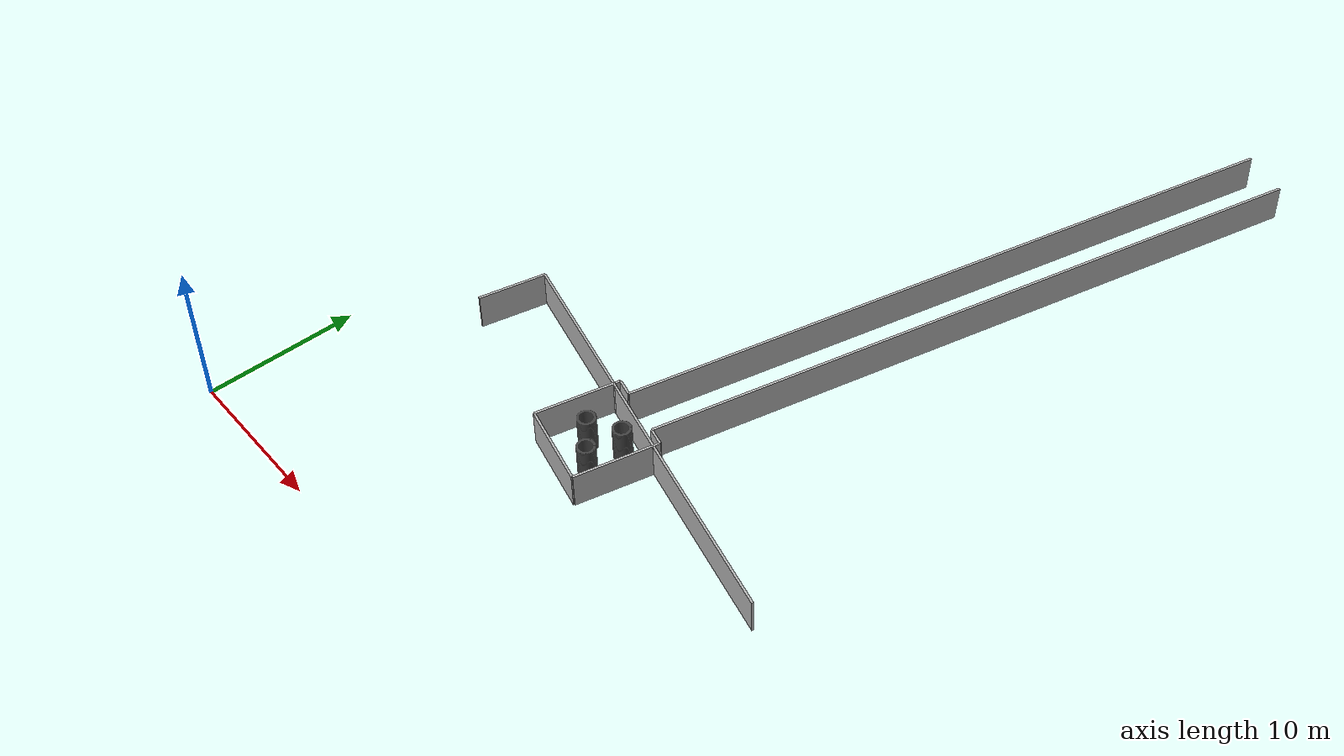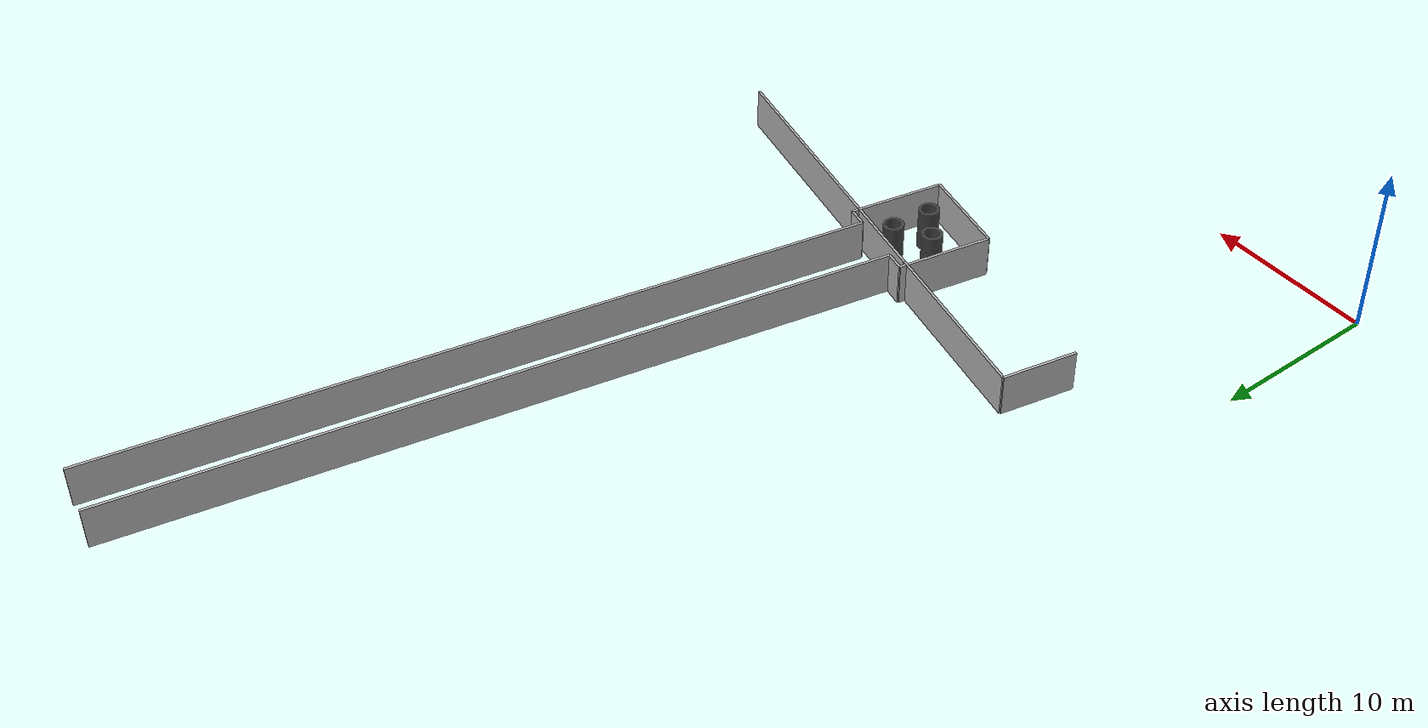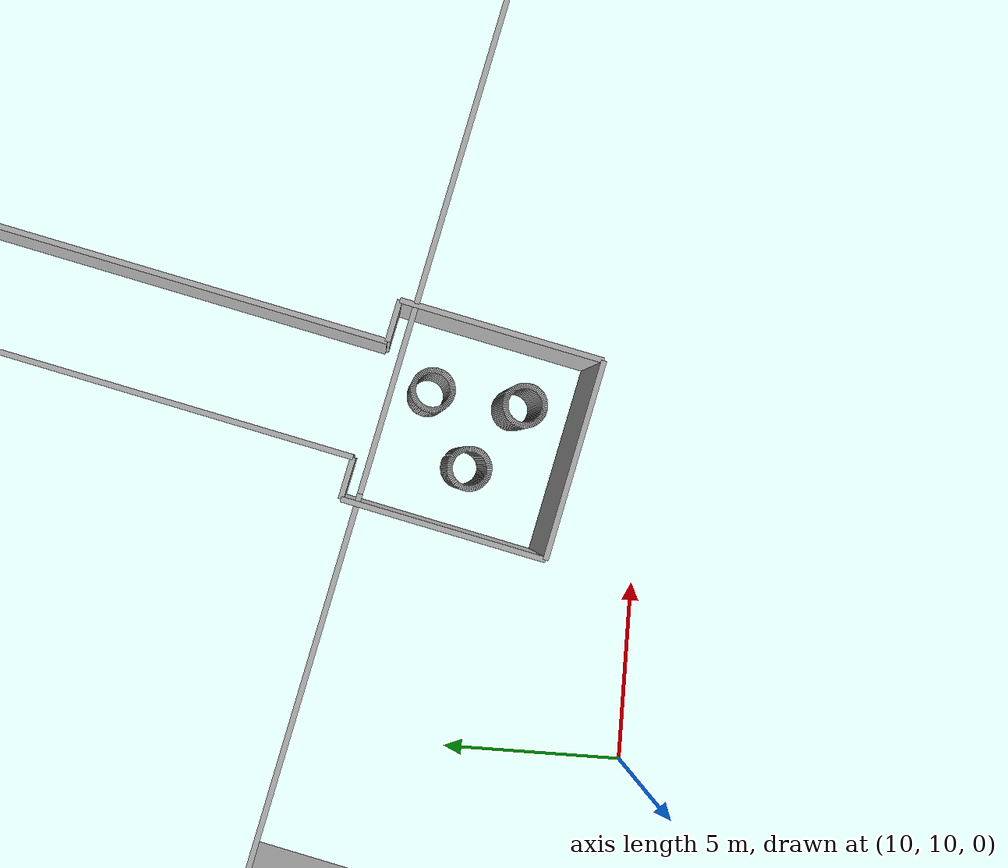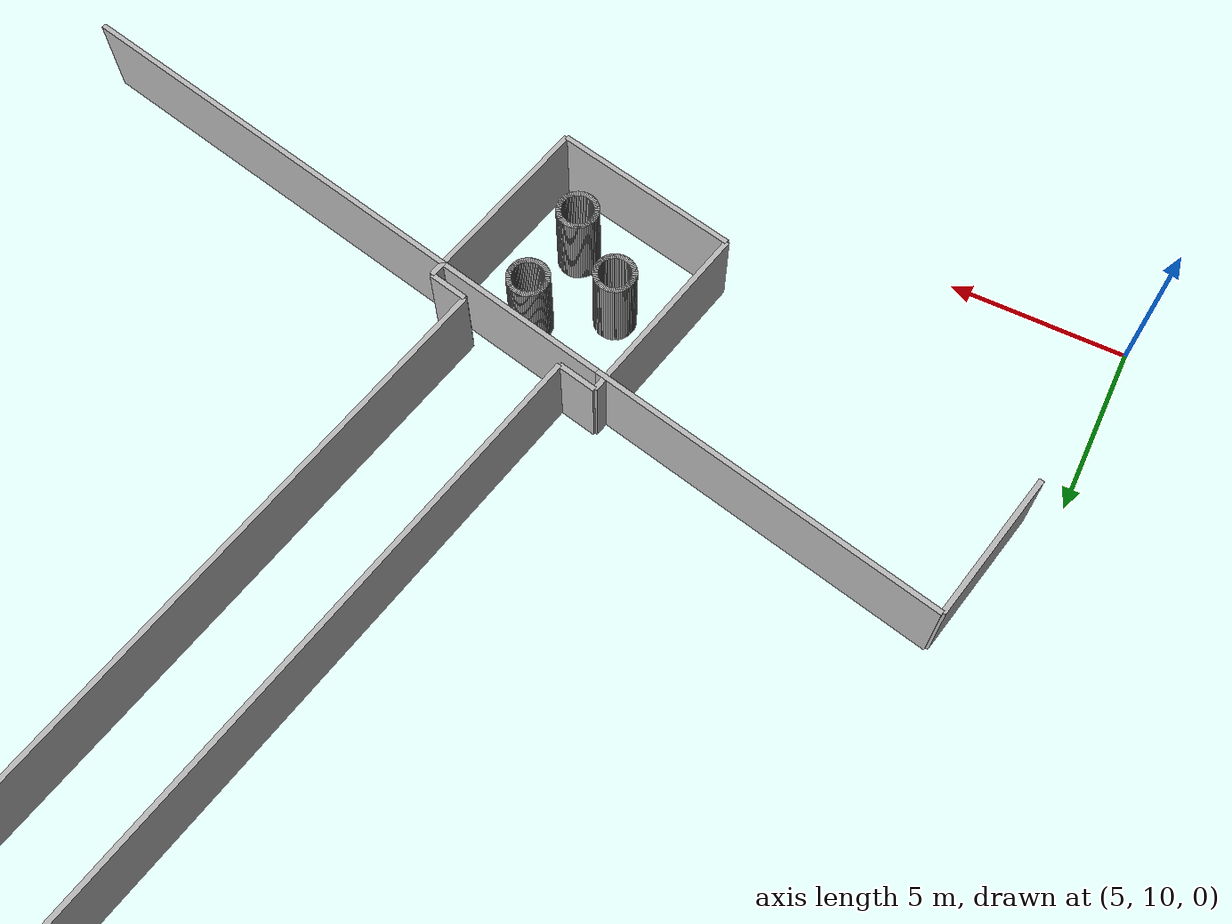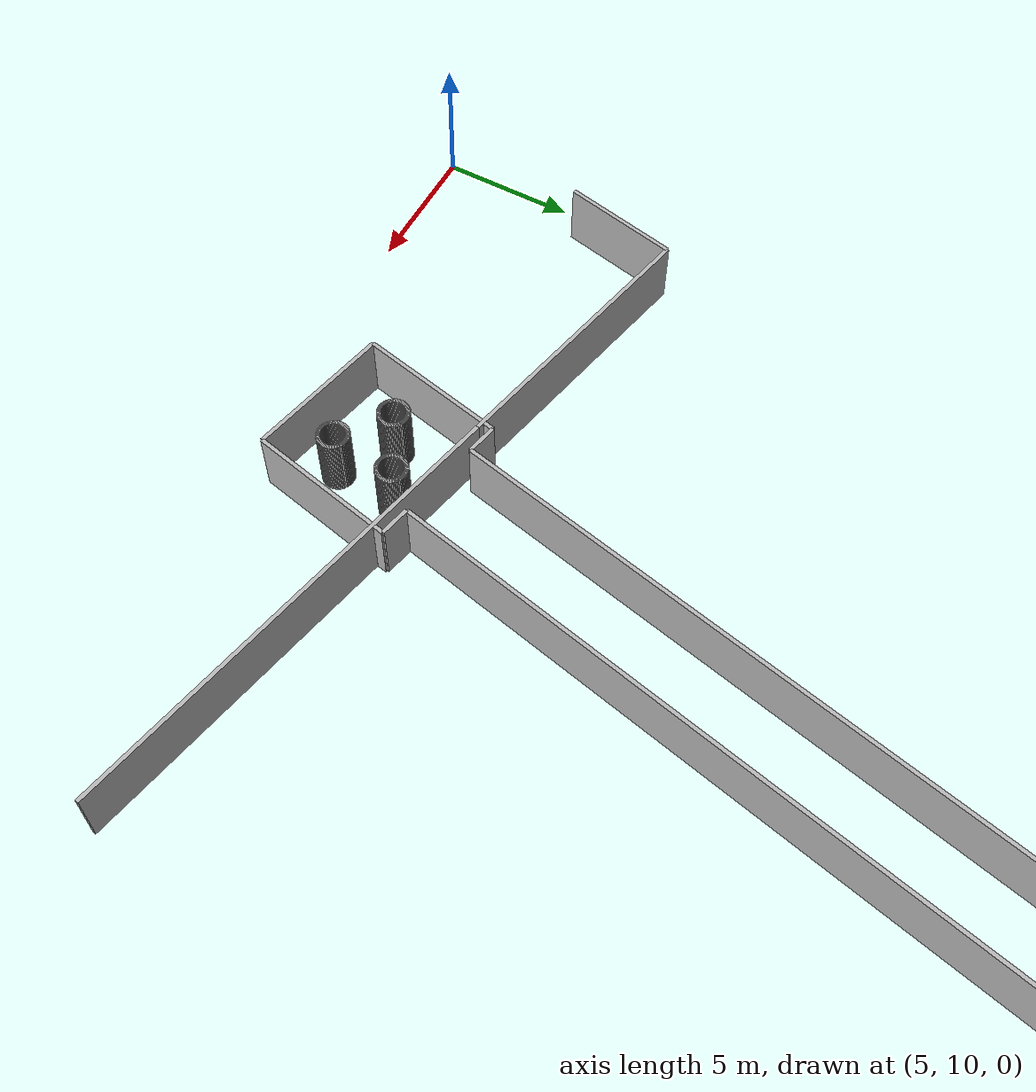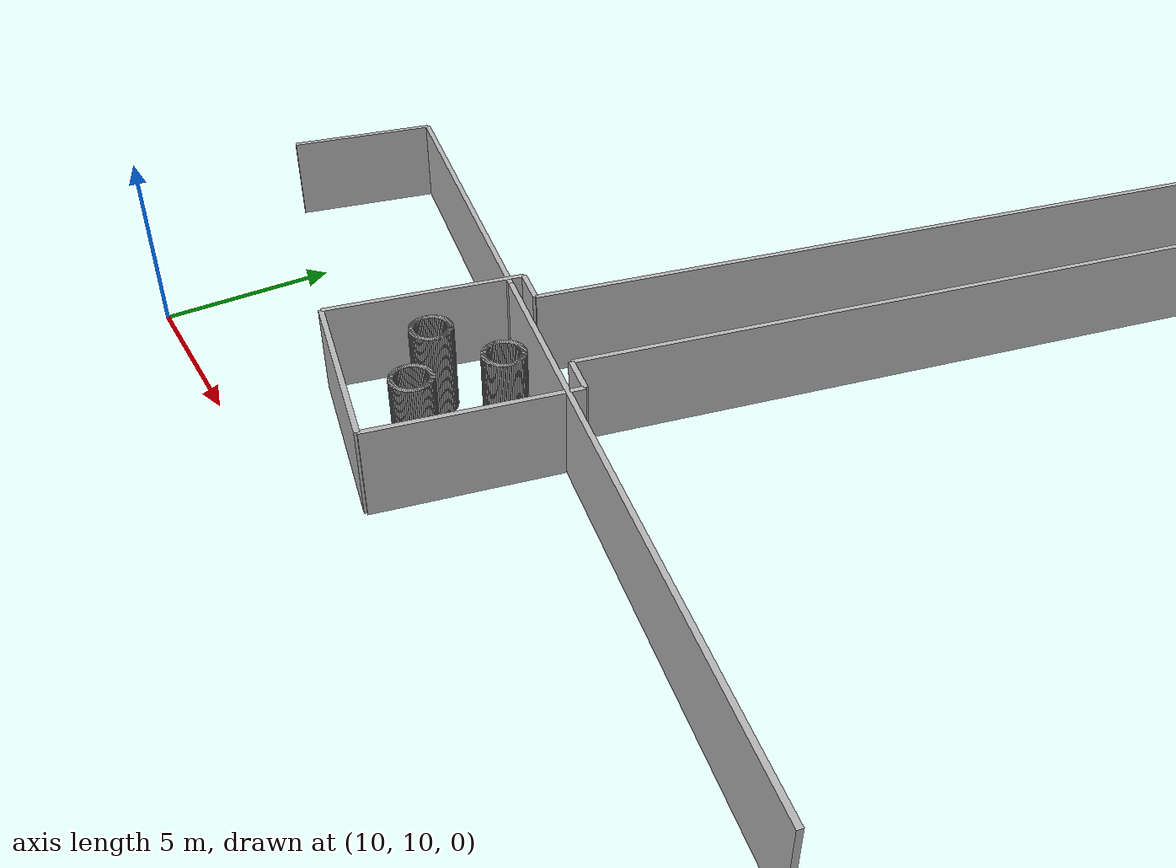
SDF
<?xml version="1.0" ?>
<sdf version="1.6">
  <model name="sps_2504">
    <pose frame="">0 0 0 0 -0 0</pose>
    <static>1</static>
    <self_collide>0</self_collide>
    <allow_auto_disable>0</allow_auto_disable>
    <link name="Wall630">
      <kinematic>0</kinematic>
      <gravity>1</gravity>
      <self_collide>0</self_collide>
      <collision name="collision">
        <geometry>
          <box>
            <size>10.4301 0.15 2.5</size>
          </box>
        </geometry>
        <pose frame="">0 0 0 0 -0 0</pose>
      </collision>
      <visual name="visual">
        <geometry>
          <box>
            <size>10.4301 0.15 2.5</size>
          </box>
        </geometry>
        <pose frame="">0 0 0 0 -0 0</pose>
        <cast_shadows>1</cast_shadows>
        <transparency>0.0</transparency>
      </visual>
      <pose frame="">11.9388 19.0019 1.25 0 0 -0.21425</pose>
    </link>
    <link name="Wall631">
      <kinematic>0</kinematic>
      <gravity>1</gravity>
      <self_collide>0</self_collide>
      <collision name="collision">
        <geometry>
          <box>
            <size>17.8427 0.15 2.5</size>
          </box>
        </geometry>
        <pose frame="">0 0 0 0 -0 0</pose>
      </collision>
      <visual name="visual">
        <geometry>
          <box>
            <size>17.8427 0.15 2.5</size>
          </box>
        </geometry>
        <pose frame="">0 0 0 0 -0 0</pose>
        <cast_shadows>1</cast_shadows>
        <transparency>0.0</transparency>
      </visual>
      <pose frame="">25.752 15.9963 1.25 0 0 -0.21425</pose>
    </link>
    <link name="Wall1306">
      <kinematic>0</kinematic>
      <gravity>1</gravity>
      <self_collide>0</self_collide>
      <collision name="collision">
        <geometry>
          <box>
            <size>0.0453524 0.15 2.5</size>
          </box>
        </geometry>
        <pose frame="">0 0 0 0 -0 0</pose>
      </collision>
      <visual name="visual">
        <geometry>
          <box>
            <size>0.0453524 0.15 2.5</size>
          </box>
        </geometry>
        <pose frame="">0 0 0 0 -0 0</pose>
        <cast_shadows>1</cast_shadows>
        <transparency>0.0</transparency>
      </visual>
      <pose frame="">19.9755 14.1679 1.25 0 0 -0.655614</pose>
    </link>
    <link name="Wall1307">
      <kinematic>0</kinematic>
      <gravity>1</gravity>
      <self_collide>0</self_collide>
      <collision name="collision">
        <geometry>
          <box>
            <size>0.0453186 0.15 2.5</size>
          </box>
        </geometry>
        <pose frame="">0 0 0 0 -0 0</pose>
      </collision>
      <visual name="visual">
        <geometry>
          <box>
            <size>0.0453186 0.15 2.5</size>
          </box>
        </geometry>
        <pose frame="">0 0 0 0 -0 0</pose>
        <cast_shadows>1</cast_shadows>
        <transparency>0.0</transparency>
      </visual>
      <pose frame="">20.0102 14.1388 1.25 0 0 -0.740624</pose>
    </link>
    <link name="Wall1308">
      <kinematic>0</kinematic>
      <gravity>1</gravity>
      <self_collide>0</self_collide>
      <collision name="collision">
        <geometry>
          <box>
            <size>0.0454087 0.15 2.5</size>
          </box>
        </geometry>
        <pose frame="">0 0 0 0 -0 0</pose>
      </collision>
      <visual name="visual">
        <geometry>
          <box>
            <size>0.0454087 0.15 2.5</size>
          </box>
        </geometry>
        <pose frame="">0 0 0 0 -0 0</pose>
        <cast_shadows>1</cast_shadows>
        <transparency>0.0</transparency>
      </visual>
      <pose frame="">20.0422 14.1067 1.25 0 0 -0.831987</pose>
    </link>
    <link name="Wall1309">
      <kinematic>0</kinematic>
      <gravity>1</gravity>
      <self_collide>0</self_collide>
      <collision name="collision">
        <geometry>
          <box>
            <size>0.0453637 0.15 2.5</size>
          </box>
        </geometry>
        <pose frame="">0 0 0 0 -0 0</pose>
      </collision>
      <visual name="visual">
        <geometry>
          <box>
            <size>0.0453637 0.15 2.5</size>
          </box>
        </geometry>
        <pose frame="">0 0 0 0 -0 0</pose>
        <cast_shadows>1</cast_shadows>
        <transparency>0.0</transparency>
      </visual>
      <pose frame="">20.0713 14.0719 1.25 0 0 -0.91707</pose>
    </link>
    <link name="Wall1310">
      <kinematic>0</kinematic>
      <gravity>1</gravity>
      <self_collide>0</self_collide>
      <collision name="collision">
        <geometry>
          <box>
            <size>0.045342 0.15 2.5</size>
          </box>
        </geometry>
        <pose frame="">0 0 0 0 -0 0</pose>
      </collision>
      <visual name="visual">
        <geometry>
          <box>
            <size>0.045342 0.15 2.5</size>
          </box>
        </geometry>
        <pose frame="">0 0 0 0 -0 0</pose>
        <cast_shadows>1</cast_shadows>
        <transparency>0.0</transparency>
      </visual>
      <pose frame="">20.0973 14.0348 1.25 0 0 -1.00221</pose>
    </link>
    <link name="Wall1311">
      <kinematic>0</kinematic>
      <gravity>1</gravity>
      <self_collide>0</self_collide>
      <collision name="collision">
        <geometry>
          <box>
            <size>0.0453724 0.15 2.5</size>
          </box>
        </geometry>
        <pose frame="">0 0 0 0 -0 0</pose>
      </collision>
      <visual name="visual">
        <geometry>
          <box>
            <size>0.0453724 0.15 2.5</size>
          </box>
        </geometry>
        <pose frame="">0 0 0 0 -0 0</pose>
        <cast_shadows>1</cast_shadows>
        <transparency>0.0</transparency>
      </visual>
      <pose frame="">20.12 13.9956 1.25 0 0 -1.0897</pose>
    </link>
    <link name="Wall1312">
      <kinematic>0</kinematic>
      <gravity>1</gravity>
      <self_collide>0</self_collide>
      <collision name="collision">
        <geometry>
          <box>
            <size>0.0453827 0.15 2.5</size>
          </box>
        </geometry>
        <pose frame="">0 0 0 0 -0 0</pose>
      </collision>
      <visual name="visual">
        <geometry>
          <box>
            <size>0.0453827 0.15 2.5</size>
          </box>
        </geometry>
        <pose frame="">0 0 0 0 -0 0</pose>
        <cast_shadows>1</cast_shadows>
        <transparency>0.0</transparency>
      </visual>
      <pose frame="">20.1391 13.9545 1.25 0 0 -1.1818</pose>
    </link>
    <link name="Wall1313">
      <kinematic>0</kinematic>
      <gravity>1</gravity>
      <self_collide>0</self_collide>
      <collision name="collision">
        <geometry>
          <box>
            <size>0.0453611 0.15 2.5</size>
          </box>
        </geometry>
        <pose frame="">0 0 0 0 -0 0</pose>
      </collision>
      <visual name="visual">
        <geometry>
          <box>
            <size>0.0453611 0.15 2.5</size>
          </box>
        </geometry>
        <pose frame="">0 0 0 0 -0 0</pose>
        <cast_shadows>1</cast_shadows>
        <transparency>0.0</transparency>
      </visual>
      <pose frame="">20.1546 13.9119 1.25 0 0 -1.26181</pose>
    </link>
    <link name="Wall1314">
      <kinematic>0</kinematic>
      <gravity>1</gravity>
      <self_collide>0</self_collide>
      <collision name="collision">
        <geometry>
          <box>
            <size>0.0453955 0.15 2.5</size>
          </box>
        </geometry>
        <pose frame="">0 0 0 0 -0 0</pose>
      </collision>
      <visual name="visual">
        <geometry>
          <box>
            <size>0.0453955 0.15 2.5</size>
          </box>
        </geometry>
        <pose frame="">0 0 0 0 -0 0</pose>
        <cast_shadows>1</cast_shadows>
        <transparency>0.0</transparency>
      </visual>
      <pose frame="">20.1663 13.8681 1.25 0 0 -1.35811</pose>
    </link>
    <link name="Wall1315">
      <kinematic>0</kinematic>
      <gravity>1</gravity>
      <self_collide>0</self_collide>
      <collision name="collision">
        <geometry>
          <box>
            <size>0.0453869 0.15 2.5</size>
          </box>
        </geometry>
        <pose frame="">0 0 0 0 -0 0</pose>
      </collision>
      <visual name="visual">
        <geometry>
          <box>
            <size>0.0453869 0.15 2.5</size>
          </box>
        </geometry>
        <pose frame="">0 0 0 0 -0 0</pose>
        <cast_shadows>1</cast_shadows>
        <transparency>0.0</transparency>
      </visual>
      <pose frame="">20.1741 13.8234 1.25 0 0 -1.43727</pose>
    </link>
    <link name="Wall1316">
      <kinematic>0</kinematic>
      <gravity>1</gravity>
      <self_collide>0</self_collide>
      <collision name="collision">
        <geometry>
          <box>
            <size>0.0452692 0.15 2.5</size>
          </box>
        </geometry>
        <pose frame="">0 0 0 0 -0 0</pose>
      </collision>
      <visual name="visual">
        <geometry>
          <box>
            <size>0.0452692 0.15 2.5</size>
          </box>
        </geometry>
        <pose frame="">0 0 0 0 -0 0</pose>
        <cast_shadows>1</cast_shadows>
        <transparency>0.0</transparency>
      </visual>
      <pose frame="">20.1781 13.7783 1.25 0 0 -1.52764</pose>
    </link>
    <link name="Wall1317">
      <kinematic>0</kinematic>
      <gravity>1</gravity>
      <self_collide>0</self_collide>
      <collision name="collision">
        <geometry>
          <box>
            <size>0.0454521 0.15 2.5</size>
          </box>
        </geometry>
        <pose frame="">0 0 0 0 -0 0</pose>
      </collision>
      <visual name="visual">
        <geometry>
          <box>
            <size>0.0454521 0.15 2.5</size>
          </box>
        </geometry>
        <pose frame="">0 0 0 0 -0 0</pose>
        <cast_shadows>1</cast_shadows>
        <transparency>0.0</transparency>
      </visual>
      <pose frame="">20.1781 13.733 1.25 0 0 -1.61378</pose>
    </link>
    <link name="Wall1318">
      <kinematic>0</kinematic>
      <gravity>1</gravity>
      <self_collide>0</self_collide>
      <collision name="collision">
        <geometry>
          <box>
            <size>0.0452055 0.15 2.5</size>
          </box>
        </geometry>
        <pose frame="">0 0 0 0 -0 0</pose>
      </collision>
      <visual name="visual">
        <geometry>
          <box>
            <size>0.0452055 0.15 2.5</size>
          </box>
        </geometry>
        <pose frame="">0 0 0 0 -0 0</pose>
        <cast_shadows>1</cast_shadows>
        <transparency>0.0</transparency>
      </visual>
      <pose frame="">20.1741 13.6879 1.25 0 0 -1.70486</pose>
    </link>
    <link name="Wall1319">
      <kinematic>0</kinematic>
      <gravity>1</gravity>
      <self_collide>0</self_collide>
      <collision name="collision">
        <geometry>
          <box>
            <size>0.0454345 0.15 2.5</size>
          </box>
        </geometry>
        <pose frame="">0 0 0 0 -0 0</pose>
      </collision>
      <visual name="visual">
        <geometry>
          <box>
            <size>0.0454345 0.15 2.5</size>
          </box>
        </geometry>
        <pose frame="">0 0 0 0 -0 0</pose>
        <cast_shadows>1</cast_shadows>
        <transparency>0.0</transparency>
      </visual>
      <pose frame="">20.1662 13.6433 1.25 0 0 -1.78743</pose>
    </link>
    <link name="Wall1320">
      <kinematic>0</kinematic>
      <gravity>1</gravity>
      <self_collide>0</self_collide>
      <collision name="collision">
        <geometry>
          <box>
            <size>0.0453057 0.15 2.5</size>
          </box>
        </geometry>
        <pose frame="">0 0 0 0 -0 0</pose>
      </collision>
      <visual name="visual">
        <geometry>
          <box>
            <size>0.0453057 0.15 2.5</size>
          </box>
        </geometry>
        <pose frame="">0 0 0 0 -0 0</pose>
        <cast_shadows>1</cast_shadows>
        <transparency>0.0</transparency>
      </visual>
      <pose frame="">20.1545 13.5995 1.25 0 0 -1.87593</pose>
    </link>
    <link name="Wall1321">
      <kinematic>0</kinematic>
      <gravity>1</gravity>
      <self_collide>0</self_collide>
      <collision name="collision">
        <geometry>
          <box>
            <size>0.0454525 0.15 2.5</size>
          </box>
        </geometry>
        <pose frame="">0 0 0 0 -0 0</pose>
      </collision>
      <visual name="visual">
        <geometry>
          <box>
            <size>0.0454525 0.15 2.5</size>
          </box>
        </geometry>
        <pose frame="">0 0 0 0 -0 0</pose>
        <cast_shadows>1</cast_shadows>
        <transparency>0.0</transparency>
      </visual>
      <pose frame="">20.139 13.5569 1.25 0 0 -1.96352</pose>
    </link>
    <link name="Wall1322">
      <kinematic>0</kinematic>
      <gravity>1</gravity>
      <self_collide>0</self_collide>
      <collision name="collision">
        <geometry>
          <box>
            <size>0.0453724 0.15 2.5</size>
          </box>
        </geometry>
        <pose frame="">0 0 0 0 -0 0</pose>
      </collision>
      <visual name="visual">
        <geometry>
          <box>
            <size>0.0453724 0.15 2.5</size>
          </box>
        </geometry>
        <pose frame="">0 0 0 0 -0 0</pose>
        <cast_shadows>1</cast_shadows>
        <transparency>0.0</transparency>
      </visual>
      <pose frame="">20.1198 13.5158 1.25 0 0 -2.05189</pose>
    </link>
    <link name="Wall1323">
      <kinematic>0</kinematic>
      <gravity>1</gravity>
      <self_collide>0</self_collide>
      <collision name="collision">
        <geometry>
          <box>
            <size>0.045342 0.15 2.5</size>
          </box>
        </geometry>
        <pose frame="">0 0 0 0 -0 0</pose>
      </collision>
      <visual name="visual">
        <geometry>
          <box>
            <size>0.045342 0.15 2.5</size>
          </box>
        </geometry>
        <pose frame="">0 0 0 0 -0 0</pose>
        <cast_shadows>1</cast_shadows>
        <transparency>0.0</transparency>
      </visual>
      <pose frame="">20.0971 13.4766 1.25 0 0 -2.13938</pose>
    </link>
    <link name="Wall1324">
      <kinematic>0</kinematic>
      <gravity>1</gravity>
      <self_collide>0</self_collide>
      <collision name="collision">
        <geometry>
          <box>
            <size>0.0453153 0.15 2.5</size>
          </box>
        </geometry>
        <pose frame="">0 0 0 0 -0 0</pose>
      </collision>
      <visual name="visual">
        <geometry>
          <box>
            <size>0.0453153 0.15 2.5</size>
          </box>
        </geometry>
        <pose frame="">0 0 0 0 -0 0</pose>
        <cast_shadows>1</cast_shadows>
        <transparency>0.0</transparency>
      </visual>
      <pose frame="">20.0711 13.4395 1.25 0 0 -2.22534</pose>
    </link>
    <link name="Wall1325">
      <kinematic>0</kinematic>
      <gravity>1</gravity>
      <self_collide>0</self_collide>
      <collision name="collision">
        <geometry>
          <box>
            <size>0.0453598 0.15 2.5</size>
          </box>
        </geometry>
        <pose frame="">0 0 0 0 -0 0</pose>
      </collision>
      <visual name="visual">
        <geometry>
          <box>
            <size>0.0453598 0.15 2.5</size>
          </box>
        </geometry>
        <pose frame="">0 0 0 0 -0 0</pose>
        <cast_shadows>1</cast_shadows>
        <transparency>0.0</transparency>
      </visual>
      <pose frame="">20.042 13.4048 1.25 0 0 -2.31241</pose>
    </link>
    <link name="Wall1326">
      <kinematic>0</kinematic>
      <gravity>1</gravity>
      <self_collide>0</self_collide>
      <collision name="collision">
        <geometry>
          <box>
            <size>0.0453974 0.15 2.5</size>
          </box>
        </geometry>
        <pose frame="">0 0 0 0 -0 0</pose>
      </collision>
      <visual name="visual">
        <geometry>
          <box>
            <size>0.0453974 0.15 2.5</size>
          </box>
        </geometry>
        <pose frame="">0 0 0 0 -0 0</pose>
        <cast_shadows>1</cast_shadows>
        <transparency>0.0</transparency>
      </visual>
      <pose frame="">20.0099 13.3727 1.25 0 0 -2.39709</pose>
    </link>
    <link name="Wall1327">
      <kinematic>0</kinematic>
      <gravity>1</gravity>
      <self_collide>0</self_collide>
      <collision name="collision">
        <geometry>
          <box>
            <size>0.0454008 0.15 2.5</size>
          </box>
        </geometry>
        <pose frame="">0 0 0 0 -0 0</pose>
      </collision>
      <visual name="visual">
        <geometry>
          <box>
            <size>0.0454008 0.15 2.5</size>
          </box>
        </geometry>
        <pose frame="">0 0 0 0 -0 0</pose>
        <cast_shadows>1</cast_shadows>
        <transparency>0.0</transparency>
      </visual>
      <pose frame="">19.9752 13.3435 1.25 0 0 -2.4868</pose>
    </link>
    <link name="Wall1328">
      <kinematic>0</kinematic>
      <gravity>1</gravity>
      <self_collide>0</self_collide>
      <collision name="collision">
        <geometry>
          <box>
            <size>0.0453659 0.15 2.5</size>
          </box>
        </geometry>
        <pose frame="">0 0 0 0 -0 0</pose>
      </collision>
      <visual name="visual">
        <geometry>
          <box>
            <size>0.0453659 0.15 2.5</size>
          </box>
        </geometry>
        <pose frame="">0 0 0 0 -0 0</pose>
        <cast_shadows>1</cast_shadows>
        <transparency>0.0</transparency>
      </visual>
      <pose frame="">19.938 13.3176 1.25 0 0 -2.57971</pose>
    </link>
    <link name="Wall1329">
      <kinematic>0</kinematic>
      <gravity>1</gravity>
      <self_collide>0</self_collide>
      <collision name="collision">
        <geometry>
          <box>
            <size>0.0453183 0.15 2.5</size>
          </box>
        </geometry>
        <pose frame="">0 0 0 0 -0 0</pose>
      </collision>
      <visual name="visual">
        <geometry>
          <box>
            <size>0.0453183 0.15 2.5</size>
          </box>
        </geometry>
        <pose frame="">0 0 0 0 -0 0</pose>
        <cast_shadows>1</cast_shadows>
        <transparency>0.0</transparency>
      </visual>
      <pose frame="">19.8988 13.295 1.25 0 0 -2.65987</pose>
    </link>
    <link name="Wall1330">
      <kinematic>0</kinematic>
      <gravity>1</gravity>
      <self_collide>0</self_collide>
      <collision name="collision">
        <geometry>
          <box>
            <size>0.0455089 0.15 2.5</size>
          </box>
        </geometry>
        <pose frame="">0 0 0 0 -0 0</pose>
      </collision>
      <visual name="visual">
        <geometry>
          <box>
            <size>0.0455089 0.15 2.5</size>
          </box>
        </geometry>
        <pose frame="">0 0 0 0 -0 0</pose>
        <cast_shadows>1</cast_shadows>
        <transparency>0.0</transparency>
      </visual>
      <pose frame="">19.8577 13.2758 1.25 0 0 -2.74938</pose>
    </link>
    <link name="Wall1331">
      <kinematic>0</kinematic>
      <gravity>1</gravity>
      <self_collide>0</self_collide>
      <collision name="collision">
        <geometry>
          <box>
            <size>0.0452475 0.15 2.5</size>
          </box>
        </geometry>
        <pose frame="">0 0 0 0 -0 0</pose>
      </collision>
      <visual name="visual">
        <geometry>
          <box>
            <size>0.0452475 0.15 2.5</size>
          </box>
        </geometry>
        <pose frame="">0 0 0 0 -0 0</pose>
        <cast_shadows>1</cast_shadows>
        <transparency>0.0</transparency>
      </visual>
      <pose frame="">19.8151 13.2603 1.25 0 0 -2.83605</pose>
    </link>
    <link name="Wall1332">
      <kinematic>0</kinematic>
      <gravity>1</gravity>
      <self_collide>0</self_collide>
      <collision name="collision">
        <geometry>
          <box>
            <size>0.0453285 0.15 2.5</size>
          </box>
        </geometry>
        <pose frame="">0 0 0 0 -0 0</pose>
      </collision>
      <visual name="visual">
        <geometry>
          <box>
            <size>0.0453285 0.15 2.5</size>
          </box>
        </geometry>
        <pose frame="">0 0 0 0 -0 0</pose>
        <cast_shadows>1</cast_shadows>
        <transparency>0.0</transparency>
      </visual>
      <pose frame="">19.7714 13.2486 1.25 0 0 -2.92307</pose>
    </link>
    <link name="Wall1333">
      <kinematic>0</kinematic>
      <gravity>1</gravity>
      <self_collide>0</self_collide>
      <collision name="collision">
        <geometry>
          <box>
            <size>0.0453551 0.15 2.5</size>
          </box>
        </geometry>
        <pose frame="">0 0 0 0 -0 0</pose>
      </collision>
      <visual name="visual">
        <geometry>
          <box>
            <size>0.0453551 0.15 2.5</size>
          </box>
        </geometry>
        <pose frame="">0 0 0 0 -0 0</pose>
        <cast_shadows>1</cast_shadows>
        <transparency>0.0</transparency>
      </visual>
      <pose frame="">19.7267 13.2408 1.25 0 0 -3.0134</pose>
    </link>
    <link name="Wall1334">
      <kinematic>0</kinematic>
      <gravity>1</gravity>
      <self_collide>0</self_collide>
      <collision name="collision">
        <geometry>
          <box>
            <size>0.0454521 0.15 2.5</size>
          </box>
        </geometry>
        <pose frame="">0 0 0 0 -0 0</pose>
      </collision>
      <visual name="visual">
        <geometry>
          <box>
            <size>0.0454521 0.15 2.5</size>
          </box>
        </geometry>
        <pose frame="">0 0 0 0 -0 0</pose>
        <cast_shadows>1</cast_shadows>
        <transparency>0.0</transparency>
      </visual>
      <pose frame="">19.6815 13.2369 1.25 0 0 -3.09861</pose>
    </link>
    <link name="Wall1335">
      <kinematic>0</kinematic>
      <gravity>1</gravity>
      <self_collide>0</self_collide>
      <collision name="collision">
        <geometry>
          <box>
            <size>0.0452082 0.15 2.5</size>
          </box>
        </geometry>
        <pose frame="">0 0 0 0 -0 0</pose>
      </collision>
      <visual name="visual">
        <geometry>
          <box>
            <size>0.0452082 0.15 2.5</size>
          </box>
        </geometry>
        <pose frame="">0 0 0 0 -0 0</pose>
        <cast_shadows>1</cast_shadows>
        <transparency>0.0</transparency>
      </visual>
      <pose frame="">19.6363 13.2369 1.25 0 -0 3.09838</pose>
    </link>
    <link name="Wall1336">
      <kinematic>0</kinematic>
      <gravity>1</gravity>
      <self_collide>0</self_collide>
      <collision name="collision">
        <geometry>
          <box>
            <size>0.0454156 0.15 2.5</size>
          </box>
        </geometry>
        <pose frame="">0 0 0 0 -0 0</pose>
      </collision>
      <visual name="visual">
        <geometry>
          <box>
            <size>0.0454156 0.15 2.5</size>
          </box>
        </geometry>
        <pose frame="">0 0 0 0 -0 0</pose>
        <cast_shadows>1</cast_shadows>
        <transparency>0.0</transparency>
      </visual>
      <pose frame="">19.5911 13.2408 1.25 0 -0 3.01357</pose>
    </link>
    <link name="Wall1337">
      <kinematic>0</kinematic>
      <gravity>1</gravity>
      <self_collide>0</self_collide>
      <collision name="collision">
        <geometry>
          <box>
            <size>0.0454476 0.15 2.5</size>
          </box>
        </geometry>
        <pose frame="">0 0 0 0 -0 0</pose>
      </collision>
      <visual name="visual">
        <geometry>
          <box>
            <size>0.0454476 0.15 2.5</size>
          </box>
        </geometry>
        <pose frame="">0 0 0 0 -0 0</pose>
        <cast_shadows>1</cast_shadows>
        <transparency>0.0</transparency>
      </visual>
      <pose frame="">19.5464 13.2486 1.25 0 -0 2.92365</pose>
    </link>
    <link name="Wall1338">
      <kinematic>0</kinematic>
      <gravity>1</gravity>
      <self_collide>0</self_collide>
      <collision name="collision">
        <geometry>
          <box>
            <size>0.0453611 0.15 2.5</size>
          </box>
        </geometry>
        <pose frame="">0 0 0 0 -0 0</pose>
      </collision>
      <visual name="visual">
        <geometry>
          <box>
            <size>0.0453611 0.15 2.5</size>
          </box>
        </geometry>
        <pose frame="">0 0 0 0 -0 0</pose>
        <cast_shadows>1</cast_shadows>
        <transparency>0.0</transparency>
      </visual>
      <pose frame="">19.5026 13.2604 1.25 0 -0 2.83261</pose>
    </link>
    <link name="Wall1339">
      <kinematic>0</kinematic>
      <gravity>1</gravity>
      <self_collide>0</self_collide>
      <collision name="collision">
        <geometry>
          <box>
            <size>0.0452834 0.15 2.5</size>
          </box>
        </geometry>
        <pose frame="">0 0 0 0 -0 0</pose>
      </collision>
      <visual name="visual">
        <geometry>
          <box>
            <size>0.0452834 0.15 2.5</size>
          </box>
        </geometry>
        <pose frame="">0 0 0 0 -0 0</pose>
        <cast_shadows>1</cast_shadows>
        <transparency>0.0</transparency>
      </visual>
      <pose frame="">19.4601 13.276 1.25 0 -0 2.74732</pose>
    </link>
    <link name="Wall1340">
      <kinematic>0</kinematic>
      <gravity>1</gravity>
      <self_collide>0</self_collide>
      <collision name="collision">
        <geometry>
          <box>
            <size>0.0454507 0.15 2.5</size>
          </box>
        </geometry>
        <pose frame="">0 0 0 0 -0 0</pose>
      </collision>
      <visual name="visual">
        <geometry>
          <box>
            <size>0.0454507 0.15 2.5</size>
          </box>
        </geometry>
        <pose frame="">0 0 0 0 -0 0</pose>
        <cast_shadows>1</cast_shadows>
        <transparency>0.0</transparency>
      </visual>
      <pose frame="">19.419 13.2951 1.25 0 -0 2.66593</pose>
    </link>
    <link name="Wall1341">
      <kinematic>0</kinematic>
      <gravity>1</gravity>
      <self_collide>0</self_collide>
      <collision name="collision">
        <geometry>
          <box>
            <size>0.0452906 0.15 2.5</size>
          </box>
        </geometry>
        <pose frame="">0 0 0 0 -0 0</pose>
      </collision>
      <visual name="visual">
        <geometry>
          <box>
            <size>0.0452906 0.15 2.5</size>
          </box>
        </geometry>
        <pose frame="">0 0 0 0 -0 0</pose>
        <cast_shadows>1</cast_shadows>
        <transparency>0.0</transparency>
      </visual>
      <pose frame="">19.3798 13.3177 1.25 0 -0 2.57228</pose>
    </link>
    <link name="Wall1342">
      <kinematic>0</kinematic>
      <gravity>1</gravity>
      <self_collide>0</self_collide>
      <collision name="collision">
        <geometry>
          <box>
            <size>0.0453637 0.15 2.5</size>
          </box>
        </geometry>
        <pose frame="">0 0 0 0 -0 0</pose>
      </collision>
      <visual name="visual">
        <geometry>
          <box>
            <size>0.0453637 0.15 2.5</size>
          </box>
        </geometry>
        <pose frame="">0 0 0 0 -0 0</pose>
        <cast_shadows>1</cast_shadows>
        <transparency>0.0</transparency>
      </visual>
      <pose frame="">19.3427 13.3437 1.25 0 -0 2.48787</pose>
    </link>
    <link name="Wall1343">
      <kinematic>0</kinematic>
      <gravity>1</gravity>
      <self_collide>0</self_collide>
      <collision name="collision">
        <geometry>
          <box>
            <size>0.0454388 0.15 2.5</size>
          </box>
        </geometry>
        <pose frame="">0 0 0 0 -0 0</pose>
      </collision>
      <visual name="visual">
        <geometry>
          <box>
            <size>0.0454388 0.15 2.5</size>
          </box>
        </geometry>
        <pose frame="">0 0 0 0 -0 0</pose>
        <cast_shadows>1</cast_shadows>
        <transparency>0.0</transparency>
      </visual>
      <pose frame="">19.308 13.3729 1.25 0 -0 2.3961</pose>
    </link>
    <link name="Wall1344">
      <kinematic>0</kinematic>
      <gravity>1</gravity>
      <self_collide>0</self_collide>
      <collision name="collision">
        <geometry>
          <box>
            <size>0.0453148 0.15 2.5</size>
          </box>
        </geometry>
        <pose frame="">0 0 0 0 -0 0</pose>
      </collision>
      <visual name="visual">
        <geometry>
          <box>
            <size>0.0453148 0.15 2.5</size>
          </box>
        </geometry>
        <pose frame="">0 0 0 0 -0 0</pose>
        <cast_shadows>1</cast_shadows>
        <transparency>0.0</transparency>
      </visual>
      <pose frame="">19.276 13.405 1.25 0 -0 2.31332</pose>
    </link>
    <link name="Wall1345">
      <kinematic>0</kinematic>
      <gravity>1</gravity>
      <self_collide>0</self_collide>
      <collision name="collision">
        <geometry>
          <box>
            <size>0.0453637 0.15 2.5</size>
          </box>
        </geometry>
        <pose frame="">0 0 0 0 -0 0</pose>
      </collision>
      <visual name="visual">
        <geometry>
          <box>
            <size>0.0453637 0.15 2.5</size>
          </box>
        </geometry>
        <pose frame="">0 0 0 0 -0 0</pose>
        <cast_shadows>1</cast_shadows>
        <transparency>0.0</transparency>
      </visual>
      <pose frame="">19.2468 13.4397 1.25 0 -0 2.22452</pose>
    </link>
    <link name="Wall1346">
      <kinematic>0</kinematic>
      <gravity>1</gravity>
      <self_collide>0</self_collide>
      <collision name="collision">
        <geometry>
          <box>
            <size>0.0452906 0.15 2.5</size>
          </box>
        </geometry>
        <pose frame="">0 0 0 0 -0 0</pose>
      </collision>
      <visual name="visual">
        <geometry>
          <box>
            <size>0.0452906 0.15 2.5</size>
          </box>
        </geometry>
        <pose frame="">0 0 0 0 -0 0</pose>
        <cast_shadows>1</cast_shadows>
        <transparency>0.0</transparency>
      </visual>
      <pose frame="">19.2208 13.4768 1.25 0 -0 2.14011</pose>
    </link>
    <link name="Wall1347">
      <kinematic>0</kinematic>
      <gravity>1</gravity>
      <self_collide>0</self_collide>
      <collision name="collision">
        <geometry>
          <box>
            <size>0.0455348 0.15 2.5</size>
          </box>
        </geometry>
        <pose frame="">0 0 0 0 -0 0</pose>
      </collision>
      <visual name="visual">
        <geometry>
          <box>
            <size>0.0455348 0.15 2.5</size>
          </box>
        </geometry>
        <pose frame="">0 0 0 0 -0 0</pose>
        <cast_shadows>1</cast_shadows>
        <transparency>0.0</transparency>
      </visual>
      <pose frame="">19.1981 13.5161 1.25 0 -0 2.05003</pose>
    </link>
    <link name="Wall1348">
      <kinematic>0</kinematic>
      <gravity>1</gravity>
      <self_collide>0</self_collide>
      <collision name="collision">
        <geometry>
          <box>
            <size>0.0452134 0.15 2.5</size>
          </box>
        </geometry>
        <pose frame="">0 0 0 0 -0 0</pose>
      </collision>
      <visual name="visual">
        <geometry>
          <box>
            <size>0.0452134 0.15 2.5</size>
          </box>
        </geometry>
        <pose frame="">0 0 0 0 -0 0</pose>
        <cast_shadows>1</cast_shadows>
        <transparency>0.0</transparency>
      </visual>
      <pose frame="">19.179 13.5572 1.25 0 -0 1.96133</pose>
    </link>
    <link name="Wall1349">
      <kinematic>0</kinematic>
      <gravity>1</gravity>
      <self_collide>0</self_collide>
      <collision name="collision">
        <geometry>
          <box>
            <size>0.0455355 0.15 2.5</size>
          </box>
        </geometry>
        <pose frame="">0 0 0 0 -0 0</pose>
      </collision>
      <visual name="visual">
        <geometry>
          <box>
            <size>0.0455355 0.15 2.5</size>
          </box>
        </geometry>
        <pose frame="">0 0 0 0 -0 0</pose>
        <cast_shadows>1</cast_shadows>
        <transparency>0.0</transparency>
      </visual>
      <pose frame="">19.1635 13.5998 1.25 0 -0 1.87856</pose>
    </link>
    <link name="Wall1350">
      <kinematic>0</kinematic>
      <gravity>1</gravity>
      <self_collide>0</self_collide>
      <collision name="collision">
        <geometry>
          <box>
            <size>0.0452557 0.15 2.5</size>
          </box>
        </geometry>
        <pose frame="">0 0 0 0 -0 0</pose>
      </collision>
      <visual name="visual">
        <geometry>
          <box>
            <size>0.0452557 0.15 2.5</size>
          </box>
        </geometry>
        <pose frame="">0 0 0 0 -0 0</pose>
        <cast_shadows>1</cast_shadows>
        <transparency>0.0</transparency>
      </visual>
      <pose frame="">19.1518 13.6436 1.25 0 -0 1.78829</pose>
    </link>
    <link name="Wall1351">
      <kinematic>0</kinematic>
      <gravity>1</gravity>
      <self_collide>0</self_collide>
      <collision name="collision">
        <geometry>
          <box>
            <size>0.0454156 0.15 2.5</size>
          </box>
        </geometry>
        <pose frame="">0 0 0 0 -0 0</pose>
      </collision>
      <visual name="visual">
        <geometry>
          <box>
            <size>0.0454156 0.15 2.5</size>
          </box>
        </geometry>
        <pose frame="">0 0 0 0 -0 0</pose>
        <cast_shadows>1</cast_shadows>
        <transparency>0.0</transparency>
      </visual>
      <pose frame="">19.144 13.6882 1.25 0 -0 1.69882</pose>
    </link>
    <link name="Wall1352">
      <kinematic>0</kinematic>
      <gravity>1</gravity>
      <self_collide>0</self_collide>
      <collision name="collision">
        <geometry>
          <box>
            <size>0.0452109 0.15 2.5</size>
          </box>
        </geometry>
        <pose frame="">0 0 0 0 -0 0</pose>
      </collision>
      <visual name="visual">
        <geometry>
          <box>
            <size>0.0452109 0.15 2.5</size>
          </box>
        </geometry>
        <pose frame="">0 0 0 0 -0 0</pose>
        <cast_shadows>1</cast_shadows>
        <transparency>0.0</transparency>
      </visual>
      <pose frame="">19.1401 13.7333 1.25 0 -0 1.61536</pose>
    </link>
    <link name="Wall1353">
      <kinematic>0</kinematic>
      <gravity>1</gravity>
      <self_collide>0</self_collide>
      <collision name="collision">
        <geometry>
          <box>
            <size>0.0454548 0.15 2.5</size>
          </box>
        </geometry>
        <pose frame="">0 0 0 0 -0 0</pose>
      </collision>
      <visual name="visual">
        <geometry>
          <box>
            <size>0.0454548 0.15 2.5</size>
          </box>
        </geometry>
        <pose frame="">0 0 0 0 -0 0</pose>
        <cast_shadows>1</cast_shadows>
        <transparency>0.0</transparency>
      </visual>
      <pose frame="">19.1401 13.7786 1.25 0 -0 1.52647</pose>
    </link>
    <link name="Wall1354">
      <kinematic>0</kinematic>
      <gravity>1</gravity>
      <self_collide>0</self_collide>
      <collision name="collision">
        <geometry>
          <box>
            <size>0.0453788 0.15 2.5</size>
          </box>
        </geometry>
        <pose frame="">0 0 0 0 -0 0</pose>
      </collision>
      <visual name="visual">
        <geometry>
          <box>
            <size>0.0453788 0.15 2.5</size>
          </box>
        </geometry>
        <pose frame="">0 0 0 0 -0 0</pose>
        <cast_shadows>1</cast_shadows>
        <transparency>0.0</transparency>
      </visual>
      <pose frame="">19.1441 13.8238 1.25 0 -0 1.4386</pose>
    </link>
    <link name="Wall1355">
      <kinematic>0</kinematic>
      <gravity>1</gravity>
      <self_collide>0</self_collide>
      <collision name="collision">
        <geometry>
          <box>
            <size>0.0453285 0.15 2.5</size>
          </box>
        </geometry>
        <pose frame="">0 0 0 0 -0 0</pose>
      </collision>
      <visual name="visual">
        <geometry>
          <box>
            <size>0.0453285 0.15 2.5</size>
          </box>
        </geometry>
        <pose frame="">0 0 0 0 -0 0</pose>
        <cast_shadows>1</cast_shadows>
        <transparency>0.0</transparency>
      </visual>
      <pose frame="">19.152 13.8684 1.25 0 -0 1.35227</pose>
    </link>
    <link name="Wall1356">
      <kinematic>0</kinematic>
      <gravity>1</gravity>
      <self_collide>0</self_collide>
      <collision name="collision">
        <geometry>
          <box>
            <size>0.0454622 0.15 2.5</size>
          </box>
        </geometry>
        <pose frame="">0 0 0 0 -0 0</pose>
      </collision>
      <visual name="visual">
        <geometry>
          <box>
            <size>0.0454622 0.15 2.5</size>
          </box>
        </geometry>
        <pose frame="">0 0 0 0 -0 0</pose>
        <cast_shadows>1</cast_shadows>
        <transparency>0.0</transparency>
      </visual>
      <pose frame="">19.1637 13.9122 1.25 0 -0 1.26815</pose>
    </link>
    <link name="Wall1357">
      <kinematic>0</kinematic>
      <gravity>1</gravity>
      <self_collide>0</self_collide>
      <collision name="collision">
        <geometry>
          <box>
            <size>0.0452834 0.15 2.5</size>
          </box>
        </geometry>
        <pose frame="">0 0 0 0 -0 0</pose>
      </collision>
      <visual name="visual">
        <geometry>
          <box>
            <size>0.0452834 0.15 2.5</size>
          </box>
        </geometry>
        <pose frame="">0 0 0 0 -0 0</pose>
        <cast_shadows>1</cast_shadows>
        <transparency>0.0</transparency>
      </visual>
      <pose frame="">19.1791 13.9548 1.25 0 -0 1.17652</pose>
    </link>
    <link name="Wall1358">
      <kinematic>0</kinematic>
      <gravity>1</gravity>
      <self_collide>0</self_collide>
      <collision name="collision">
        <geometry>
          <box>
            <size>0.0452338 0.15 2.5</size>
          </box>
        </geometry>
        <pose frame="">0 0 0 0 -0 0</pose>
      </collision>
      <visual name="visual">
        <geometry>
          <box>
            <size>0.0452338 0.15 2.5</size>
          </box>
        </geometry>
        <pose frame="">0 0 0 0 -0 0</pose>
        <cast_shadows>1</cast_shadows>
        <transparency>0.0</transparency>
      </visual>
      <pose frame="">19.1982 13.9958 1.25 0 -0 1.09267</pose>
    </link>
    <link name="Wall1359">
      <kinematic>0</kinematic>
      <gravity>1</gravity>
      <self_collide>0</self_collide>
      <collision name="collision">
        <geometry>
          <box>
            <size>0.0455949 0.15 2.5</size>
          </box>
        </geometry>
        <pose frame="">0 0 0 0 -0 0</pose>
      </collision>
      <visual name="visual">
        <geometry>
          <box>
            <size>0.0455949 0.15 2.5</size>
          </box>
        </geometry>
        <pose frame="">0 0 0 0 -0 0</pose>
        <cast_shadows>1</cast_shadows>
        <transparency>0.0</transparency>
      </visual>
      <pose frame="">19.2209 14.0351 1.25 0 -0 1.00099</pose>
    </link>
    <link name="Wall1360">
      <kinematic>0</kinematic>
      <gravity>1</gravity>
      <self_collide>0</self_collide>
      <collision name="collision">
        <geometry>
          <box>
            <size>0.0453637 0.15 2.5</size>
          </box>
        </geometry>
        <pose frame="">0 0 0 0 -0 0</pose>
      </collision>
      <visual name="visual">
        <geometry>
          <box>
            <size>0.0453637 0.15 2.5</size>
          </box>
        </geometry>
        <pose frame="">0 0 0 0 -0 0</pose>
        <cast_shadows>1</cast_shadows>
        <transparency>0.0</transparency>
      </visual>
      <pose frame="">19.247 14.0723 1.25 0 -0 0.91707</pose>
    </link>
    <link name="Wall1361">
      <kinematic>0</kinematic>
      <gravity>1</gravity>
      <self_collide>0</self_collide>
      <collision name="collision">
        <geometry>
          <box>
            <size>0.0453148 0.15 2.5</size>
          </box>
        </geometry>
        <pose frame="">0 0 0 0 -0 0</pose>
      </collision>
      <visual name="visual">
        <geometry>
          <box>
            <size>0.0453148 0.15 2.5</size>
          </box>
        </geometry>
        <pose frame="">0 0 0 0 -0 0</pose>
        <cast_shadows>1</cast_shadows>
        <transparency>0.0</transparency>
      </visual>
      <pose frame="">19.2761 14.107 1.25 0 -0 0.82827</pose>
    </link>
    <link name="Wall1362">
      <kinematic>0</kinematic>
      <gravity>1</gravity>
      <self_collide>0</self_collide>
      <collision name="collision">
        <geometry>
          <box>
            <size>0.0453148 0.15 2.5</size>
          </box>
        </geometry>
        <pose frame="">0 0 0 0 -0 0</pose>
      </collision>
      <visual name="visual">
        <geometry>
          <box>
            <size>0.0453148 0.15 2.5</size>
          </box>
        </geometry>
        <pose frame="">0 0 0 0 -0 0</pose>
        <cast_shadows>1</cast_shadows>
        <transparency>0.0</transparency>
      </visual>
      <pose frame="">19.3082 14.139 1.25 0 -0 0.742526</pose>
    </link>
    <link name="Wall1363">
      <kinematic>0</kinematic>
      <gravity>1</gravity>
      <self_collide>0</self_collide>
      <collision name="collision">
        <geometry>
          <box>
            <size>0.0453637 0.15 2.5</size>
          </box>
        </geometry>
        <pose frame="">0 0 0 0 -0 0</pose>
      </collision>
      <visual name="visual">
        <geometry>
          <box>
            <size>0.0453637 0.15 2.5</size>
          </box>
        </geometry>
        <pose frame="">0 0 0 0 -0 0</pose>
        <cast_shadows>1</cast_shadows>
        <transparency>0.0</transparency>
      </visual>
      <pose frame="">19.3429 14.1681 1.25 0 -0 0.653727</pose>
    </link>
    <link name="Wall1364">
      <kinematic>0</kinematic>
      <gravity>1</gravity>
      <self_collide>0</self_collide>
      <collision name="collision">
        <geometry>
          <box>
            <size>0.0454964 0.15 2.5</size>
          </box>
        </geometry>
        <pose frame="">0 0 0 0 -0 0</pose>
      </collision>
      <visual name="visual">
        <geometry>
          <box>
            <size>0.0454964 0.15 2.5</size>
          </box>
        </geometry>
        <pose frame="">0 0 0 0 -0 0</pose>
        <cast_shadows>1</cast_shadows>
        <transparency>0.0</transparency>
      </visual>
      <pose frame="">19.3801 14.1941 1.25 0 -0 0.566421</pose>
    </link>
    <link name="Wall1365">
      <kinematic>0</kinematic>
      <gravity>1</gravity>
      <self_collide>0</self_collide>
      <collision name="collision">
        <geometry>
          <box>
            <size>0.04526 0.15 2.5</size>
          </box>
        </geometry>
        <pose frame="">0 0 0 0 -0 0</pose>
      </collision>
      <visual name="visual">
        <geometry>
          <box>
            <size>0.04526 0.15 2.5</size>
          </box>
        </geometry>
        <pose frame="">0 0 0 0 -0 0</pose>
        <cast_shadows>1</cast_shadows>
        <transparency>0.0</transparency>
      </visual>
      <pose frame="">19.4194 14.2167 1.25 0 -0 0.476313</pose>
    </link>
    <link name="Wall1366">
      <kinematic>0</kinematic>
      <gravity>1</gravity>
      <self_collide>0</self_collide>
      <collision name="collision">
        <geometry>
          <box>
            <size>0.0453069 0.15 2.5</size>
          </box>
        </geometry>
        <pose frame="">0 0 0 0 -0 0</pose>
      </collision>
      <visual name="visual">
        <geometry>
          <box>
            <size>0.0453069 0.15 2.5</size>
          </box>
        </geometry>
        <pose frame="">0 0 0 0 -0 0</pose>
        <cast_shadows>1</cast_shadows>
        <transparency>0.0</transparency>
      </visual>
      <pose frame="">19.4604 14.2358 1.25 0 -0 0.395517</pose>
    </link>
    <link name="Wall1367">
      <kinematic>0</kinematic>
      <gravity>1</gravity>
      <self_collide>0</self_collide>
      <collision name="collision">
        <geometry>
          <box>
            <size>0.0454622 0.15 2.5</size>
          </box>
        </geometry>
        <pose frame="">0 0 0 0 -0 0</pose>
      </collision>
      <visual name="visual">
        <geometry>
          <box>
            <size>0.0454622 0.15 2.5</size>
          </box>
        </geometry>
        <pose frame="">0 0 0 0 -0 0</pose>
        <cast_shadows>1</cast_shadows>
        <transparency>0.0</transparency>
      </visual>
      <pose frame="">19.503 14.2513 1.25 0 -0 0.302645</pose>
    </link>
    <link name="Wall1368">
      <kinematic>0</kinematic>
      <gravity>1</gravity>
      <self_collide>0</self_collide>
      <collision name="collision">
        <geometry>
          <box>
            <size>0.0452689 0.15 2.5</size>
          </box>
        </geometry>
        <pose frame="">0 0 0 0 -0 0</pose>
      </collision>
      <visual name="visual">
        <geometry>
          <box>
            <size>0.0452689 0.15 2.5</size>
          </box>
        </geometry>
        <pose frame="">0 0 0 0 -0 0</pose>
        <cast_shadows>1</cast_shadows>
        <transparency>0.0</transparency>
      </visual>
      <pose frame="">19.5468 14.263 1.25 0 -0 0.218815</pose>
    </link>
    <link name="Wall1369">
      <kinematic>0</kinematic>
      <gravity>1</gravity>
      <self_collide>0</self_collide>
      <collision name="collision">
        <geometry>
          <box>
            <size>0.0453788 0.15 2.5</size>
          </box>
        </geometry>
        <pose frame="">0 0 0 0 -0 0</pose>
      </collision>
      <visual name="visual">
        <geometry>
          <box>
            <size>0.0453788 0.15 2.5</size>
          </box>
        </geometry>
        <pose frame="">0 0 0 0 -0 0</pose>
        <cast_shadows>1</cast_shadows>
        <transparency>0.0</transparency>
      </visual>
      <pose frame="">19.5914 14.2709 1.25 0 -0 0.132196</pose>
    </link>
    <link name="Wall1370">
      <kinematic>0</kinematic>
      <gravity>1</gravity>
      <self_collide>0</self_collide>
      <collision name="collision">
        <geometry>
          <box>
            <size>0.0454548 0.15 2.5</size>
          </box>
        </geometry>
        <pose frame="">0 0 0 0 -0 0</pose>
      </collision>
      <visual name="visual">
        <geometry>
          <box>
            <size>0.0454548 0.15 2.5</size>
          </box>
        </geometry>
        <pose frame="">0 0 0 0 -0 0</pose>
        <cast_shadows>1</cast_shadows>
        <transparency>0.0</transparency>
      </visual>
      <pose frame="">19.6366 14.2749 1.25 0 -0 0.0443258</pose>
    </link>
    <link name="Wall1371">
      <kinematic>0</kinematic>
      <gravity>1</gravity>
      <self_collide>0</self_collide>
      <collision name="collision">
        <geometry>
          <box>
            <size>0.0452109 0.15 2.5</size>
          </box>
        </geometry>
        <pose frame="">0 0 0 0 -0 0</pose>
      </collision>
      <visual name="visual">
        <geometry>
          <box>
            <size>0.0452109 0.15 2.5</size>
          </box>
        </geometry>
        <pose frame="">0 0 0 0 -0 0</pose>
        <cast_shadows>1</cast_shadows>
        <transparency>0.0</transparency>
      </visual>
      <pose frame="">19.6818 14.2749 1.25 0 0 -0.0445651</pose>
    </link>
    <link name="Wall1372">
      <kinematic>0</kinematic>
      <gravity>1</gravity>
      <self_collide>0</self_collide>
      <collision name="collision">
        <geometry>
          <box>
            <size>0.0454394 0.15 2.5</size>
          </box>
        </geometry>
        <pose frame="">0 0 0 0 -0 0</pose>
      </collision>
      <visual name="visual">
        <geometry>
          <box>
            <size>0.0454394 0.15 2.5</size>
          </box>
        </geometry>
        <pose frame="">0 0 0 0 -0 0</pose>
        <cast_shadows>1</cast_shadows>
        <transparency>0.0</transparency>
      </visual>
      <pose frame="">19.727 14.2709 1.25 0 0 -0.132019</pose>
    </link>
    <link name="Wall1373">
      <kinematic>0</kinematic>
      <gravity>1</gravity>
      <self_collide>0</self_collide>
      <collision name="collision">
        <geometry>
          <box>
            <size>0.0454476 0.15 2.5</size>
          </box>
        </geometry>
        <pose frame="">0 0 0 0 -0 0</pose>
      </collision>
      <visual name="visual">
        <geometry>
          <box>
            <size>0.0454476 0.15 2.5</size>
          </box>
        </geometry>
        <pose frame="">0 0 0 0 -0 0</pose>
        <cast_shadows>1</cast_shadows>
        <transparency>0.0</transparency>
      </visual>
      <pose frame="">19.7717 14.263 1.25 0 0 -0.217941</pose>
    </link>
    <link name="Wall1374">
      <kinematic>0</kinematic>
      <gravity>1</gravity>
      <self_collide>0</self_collide>
      <collision name="collision">
        <geometry>
          <box>
            <size>0.0452874 0.15 2.5</size>
          </box>
        </geometry>
        <pose frame="">0 0 0 0 -0 0</pose>
      </collision>
      <visual name="visual">
        <geometry>
          <box>
            <size>0.0452874 0.15 2.5</size>
          </box>
        </geometry>
        <pose frame="">0 0 0 0 -0 0</pose>
        <cast_shadows>1</cast_shadows>
        <transparency>0.0</transparency>
      </visual>
      <pose frame="">19.8155 14.2513 1.25 0 0 -0.30385</pose>
    </link>
    <link name="Wall1375">
      <kinematic>0</kinematic>
      <gravity>1</gravity>
      <self_collide>0</self_collide>
      <collision name="collision">
        <geometry>
          <box>
            <size>0.0453069 0.15 2.5</size>
          </box>
        </geometry>
        <pose frame="">0 0 0 0 -0 0</pose>
      </collision>
      <visual name="visual">
        <geometry>
          <box>
            <size>0.0453069 0.15 2.5</size>
          </box>
        </geometry>
        <pose frame="">0 0 0 0 -0 0</pose>
        <cast_shadows>1</cast_shadows>
        <transparency>0.0</transparency>
      </visual>
      <pose frame="">19.858 14.2358 1.25 0 0 -0.395517</pose>
    </link>
    <link name="Wall1376">
      <kinematic>0</kinematic>
      <gravity>1</gravity>
      <self_collide>0</self_collide>
      <collision name="collision">
        <geometry>
          <box>
            <size>0.0455348 0.15 2.5</size>
          </box>
        </geometry>
        <pose frame="">0 0 0 0 -0 0</pose>
      </collision>
      <visual name="visual">
        <geometry>
          <box>
            <size>0.0455348 0.15 2.5</size>
          </box>
        </geometry>
        <pose frame="">0 0 0 0 -0 0</pose>
        <cast_shadows>1</cast_shadows>
        <transparency>0.0</transparency>
      </visual>
      <pose frame="">19.8991 14.2166 1.25 0 0 -0.479234</pose>
    </link>
    <link name="Wall1903">
      <kinematic>0</kinematic>
      <gravity>1</gravity>
      <self_collide>0</self_collide>
      <collision name="collision">
        <geometry>
          <box>
            <size>0.0453637 0.15 2.5</size>
          </box>
        </geometry>
        <pose frame="">0 0 0 0 -0 0</pose>
      </collision>
      <visual name="visual">
        <geometry>
          <box>
            <size>0.0453637 0.15 2.5</size>
          </box>
        </geometry>
        <pose frame="">0 0 0 0 -0 0</pose>
        <cast_shadows>1</cast_shadows>
        <transparency>0.0</transparency>
      </visual>
      <pose frame="">20.1989 16.6063 1.25 0 0 -0.653727</pose>
    </link>
    <link name="Wall1904">
      <kinematic>0</kinematic>
      <gravity>1</gravity>
      <self_collide>0</self_collide>
      <collision name="collision">
        <geometry>
          <box>
            <size>0.0453974 0.15 2.5</size>
          </box>
        </geometry>
        <pose frame="">0 0 0 0 -0 0</pose>
      </collision>
      <visual name="visual">
        <geometry>
          <box>
            <size>0.0453974 0.15 2.5</size>
          </box>
        </geometry>
        <pose frame="">0 0 0 0 -0 0</pose>
        <cast_shadows>1</cast_shadows>
        <transparency>0.0</transparency>
      </visual>
      <pose frame="">20.2336 16.5771 1.25 0 0 -0.744508</pose>
    </link>
    <link name="Wall1905">
      <kinematic>0</kinematic>
      <gravity>1</gravity>
      <self_collide>0</self_collide>
      <collision name="collision">
        <geometry>
          <box>
            <size>0.0453186 0.15 2.5</size>
          </box>
        </geometry>
        <pose frame="">0 0 0 0 -0 0</pose>
      </collision>
      <visual name="visual">
        <geometry>
          <box>
            <size>0.0453186 0.15 2.5</size>
          </box>
        </geometry>
        <pose frame="">0 0 0 0 -0 0</pose>
        <cast_shadows>1</cast_shadows>
        <transparency>0.0</transparency>
      </visual>
      <pose frame="">20.2656 16.545 1.25 0 0 -0.830173</pose>
    </link>
    <link name="Wall1906">
      <kinematic>0</kinematic>
      <gravity>1</gravity>
      <self_collide>0</self_collide>
      <collision name="collision">
        <geometry>
          <box>
            <size>0.0453637 0.15 2.5</size>
          </box>
        </geometry>
        <pose frame="">0 0 0 0 -0 0</pose>
      </collision>
      <visual name="visual">
        <geometry>
          <box>
            <size>0.0453637 0.15 2.5</size>
          </box>
        </geometry>
        <pose frame="">0 0 0 0 -0 0</pose>
        <cast_shadows>1</cast_shadows>
        <transparency>0.0</transparency>
      </visual>
      <pose frame="">20.2946 16.5103 1.25 0 0 -0.91707</pose>
    </link>
    <link name="Wall1907">
      <kinematic>0</kinematic>
      <gravity>1</gravity>
      <self_collide>0</self_collide>
      <collision name="collision">
        <geometry>
          <box>
            <size>0.0452906 0.15 2.5</size>
          </box>
        </geometry>
        <pose frame="">0 0 0 0 -0 0</pose>
      </collision>
      <visual name="visual">
        <geometry>
          <box>
            <size>0.0452906 0.15 2.5</size>
          </box>
        </geometry>
        <pose frame="">0 0 0 0 -0 0</pose>
        <cast_shadows>1</cast_shadows>
        <transparency>0.0</transparency>
      </visual>
      <pose frame="">20.3206 16.4732 1.25 0 0 -1.00148</pose>
    </link>
    <link name="Wall1908">
      <kinematic>0</kinematic>
      <gravity>1</gravity>
      <self_collide>0</self_collide>
      <collision name="collision">
        <geometry>
          <box>
            <size>0.0453724 0.15 2.5</size>
          </box>
        </geometry>
        <pose frame="">0 0 0 0 -0 0</pose>
      </collision>
      <visual name="visual">
        <geometry>
          <box>
            <size>0.0453724 0.15 2.5</size>
          </box>
        </geometry>
        <pose frame="">0 0 0 0 -0 0</pose>
        <cast_shadows>1</cast_shadows>
        <transparency>0.0</transparency>
      </visual>
      <pose frame="">20.3433 16.434 1.25 0 0 -1.0897</pose>
    </link>
    <link name="Wall1909">
      <kinematic>0</kinematic>
      <gravity>1</gravity>
      <self_collide>0</self_collide>
      <collision name="collision">
        <geometry>
          <box>
            <size>0.0454525 0.15 2.5</size>
          </box>
        </geometry>
        <pose frame="">0 0 0 0 -0 0</pose>
      </collision>
      <visual name="visual">
        <geometry>
          <box>
            <size>0.0454525 0.15 2.5</size>
          </box>
        </geometry>
        <pose frame="">0 0 0 0 -0 0</pose>
        <cast_shadows>1</cast_shadows>
        <transparency>0.0</transparency>
      </visual>
      <pose frame="">20.3625 16.3929 1.25 0 0 -1.17807</pose>
    </link>
    <link name="Wall1910">
      <kinematic>0</kinematic>
      <gravity>1</gravity>
      <self_collide>0</self_collide>
      <collision name="collision">
        <geometry>
          <box>
            <size>0.0453057 0.15 2.5</size>
          </box>
        </geometry>
        <pose frame="">0 0 0 0 -0 0</pose>
      </collision>
      <visual name="visual">
        <geometry>
          <box>
            <size>0.0453057 0.15 2.5</size>
          </box>
        </geometry>
        <pose frame="">0 0 0 0 -0 0</pose>
        <cast_shadows>1</cast_shadows>
        <transparency>0.0</transparency>
      </visual>
      <pose frame="">20.378 16.3503 1.25 0 0 -1.26566</pose>
    </link>
    <link name="Wall1911">
      <kinematic>0</kinematic>
      <gravity>1</gravity>
      <self_collide>0</self_collide>
      <collision name="collision">
        <geometry>
          <box>
            <size>0.0454476 0.15 2.5</size>
          </box>
        </geometry>
        <pose frame="">0 0 0 0 -0 0</pose>
      </collision>
      <visual name="visual">
        <geometry>
          <box>
            <size>0.0454476 0.15 2.5</size>
          </box>
        </geometry>
        <pose frame="">0 0 0 0 -0 0</pose>
        <cast_shadows>1</cast_shadows>
        <transparency>0.0</transparency>
      </visual>
      <pose frame="">20.3898 16.3065 1.25 0 0 -1.35286</pose>
    </link>
    <link name="Wall1912">
      <kinematic>0</kinematic>
      <gravity>1</gravity>
      <self_collide>0</self_collide>
      <collision name="collision">
        <geometry>
          <box>
            <size>0.0454156 0.15 2.5</size>
          </box>
        </geometry>
        <pose frame="">0 0 0 0 -0 0</pose>
      </collision>
      <visual name="visual">
        <geometry>
          <box>
            <size>0.0454156 0.15 2.5</size>
          </box>
        </geometry>
        <pose frame="">0 0 0 0 -0 0</pose>
        <cast_shadows>1</cast_shadows>
        <transparency>0.0</transparency>
      </visual>
      <pose frame="">20.3976 16.2618 1.25 0 0 -1.44277</pose>
    </link>
    <link name="Wall1913">
      <kinematic>0</kinematic>
      <gravity>1</gravity>
      <self_collide>0</self_collide>
      <collision name="collision">
        <geometry>
          <box>
            <size>0.0452082 0.15 2.5</size>
          </box>
        </geometry>
        <pose frame="">0 0 0 0 -0 0</pose>
      </collision>
      <visual name="visual">
        <geometry>
          <box>
            <size>0.0452082 0.15 2.5</size>
          </box>
        </geometry>
        <pose frame="">0 0 0 0 -0 0</pose>
        <cast_shadows>1</cast_shadows>
        <transparency>0.0</transparency>
      </visual>
      <pose frame="">20.4015 16.2167 1.25 0 0 -1.52758</pose>
    </link>
    <link name="Wall1914">
      <kinematic>0</kinematic>
      <gravity>1</gravity>
      <self_collide>0</self_collide>
      <collision name="collision">
        <geometry>
          <box>
            <size>0.0454521 0.15 2.5</size>
          </box>
        </geometry>
        <pose frame="">0 0 0 0 -0 0</pose>
      </collision>
      <visual name="visual">
        <geometry>
          <box>
            <size>0.0454521 0.15 2.5</size>
          </box>
        </geometry>
        <pose frame="">0 0 0 0 -0 0</pose>
        <cast_shadows>1</cast_shadows>
        <transparency>0.0</transparency>
      </visual>
      <pose frame="">20.4015 16.1714 1.25 0 0 -1.61378</pose>
    </link>
    <link name="Wall1915">
      <kinematic>0</kinematic>
      <gravity>1</gravity>
      <self_collide>0</self_collide>
      <collision name="collision">
        <geometry>
          <box>
            <size>0.0453869 0.15 2.5</size>
          </box>
        </geometry>
        <pose frame="">0 0 0 0 -0 0</pose>
      </collision>
      <visual name="visual">
        <geometry>
          <box>
            <size>0.0453869 0.15 2.5</size>
          </box>
        </geometry>
        <pose frame="">0 0 0 0 -0 0</pose>
        <cast_shadows>1</cast_shadows>
        <transparency>0.0</transparency>
      </visual>
      <pose frame="">20.3975 16.1262 1.25 0 0 -1.70433</pose>
    </link>
    <link name="Wall1916">
      <kinematic>0</kinematic>
      <gravity>1</gravity>
      <self_collide>0</self_collide>
      <collision name="collision">
        <geometry>
          <box>
            <size>0.0453153 0.15 2.5</size>
          </box>
        </geometry>
        <pose frame="">0 0 0 0 -0 0</pose>
      </collision>
      <visual name="visual">
        <geometry>
          <box>
            <size>0.0453153 0.15 2.5</size>
          </box>
        </geometry>
        <pose frame="">0 0 0 0 -0 0</pose>
        <cast_shadows>1</cast_shadows>
        <transparency>0.0</transparency>
      </visual>
      <pose frame="">20.3895 16.0816 1.25 0 0 -1.788</pose>
    </link>
    <link name="Wall1917">
      <kinematic>0</kinematic>
      <gravity>1</gravity>
      <self_collide>0</self_collide>
      <collision name="collision">
        <geometry>
          <box>
            <size>0.0454804 0.15 2.5</size>
          </box>
        </geometry>
        <pose frame="">0 0 0 0 -0 0</pose>
      </collision>
      <visual name="visual">
        <geometry>
          <box>
            <size>0.0454804 0.15 2.5</size>
          </box>
        </geometry>
        <pose frame="">0 0 0 0 -0 0</pose>
        <cast_shadows>1</cast_shadows>
        <transparency>0.0</transparency>
      </visual>
      <pose frame="">20.3779 16.0378 1.25 0 0 -1.87472</pose>
    </link>
    <link name="Wall1918">
      <kinematic>0</kinematic>
      <gravity>1</gravity>
      <self_collide>0</self_collide>
      <collision name="collision">
        <geometry>
          <box>
            <size>0.0452271 0.15 2.5</size>
          </box>
        </geometry>
        <pose frame="">0 0 0 0 -0 0</pose>
      </collision>
      <visual name="visual">
        <geometry>
          <box>
            <size>0.0452271 0.15 2.5</size>
          </box>
        </geometry>
        <pose frame="">0 0 0 0 -0 0</pose>
        <cast_shadows>1</cast_shadows>
        <transparency>0.0</transparency>
      </visual>
      <pose frame="">20.3624 15.9952 1.25 0 0 -1.96559</pose>
    </link>
    <link name="Wall1919">
      <kinematic>0</kinematic>
      <gravity>1</gravity>
      <self_collide>0</self_collide>
      <collision name="collision">
        <geometry>
          <box>
            <size>0.0453724 0.15 2.5</size>
          </box>
        </geometry>
        <pose frame="">0 0 0 0 -0 0</pose>
      </collision>
      <visual name="visual">
        <geometry>
          <box>
            <size>0.0453724 0.15 2.5</size>
          </box>
        </geometry>
        <pose frame="">0 0 0 0 -0 0</pose>
        <cast_shadows>1</cast_shadows>
        <transparency>0.0</transparency>
      </visual>
      <pose frame="">20.3432 15.9542 1.25 0 0 -2.05189</pose>
    </link>
    <link name="Wall1920">
      <kinematic>0</kinematic>
      <gravity>1</gravity>
      <self_collide>0</self_collide>
      <collision name="collision">
        <geometry>
          <box>
            <size>0.0452437 0.15 2.5</size>
          </box>
        </geometry>
        <pose frame="">0 0 0 0 -0 0</pose>
      </collision>
      <visual name="visual">
        <geometry>
          <box>
            <size>0.0452437 0.15 2.5</size>
          </box>
        </geometry>
        <pose frame="">0 0 0 0 -0 0</pose>
        <cast_shadows>1</cast_shadows>
        <transparency>0.0</transparency>
      </visual>
      <pose frame="">20.3205 15.915 1.25 0 0 -2.13597</pose>
    </link>
    <link name="Wall1921">
      <kinematic>0</kinematic>
      <gravity>1</gravity>
      <self_collide>0</self_collide>
      <collision name="collision">
        <geometry>
          <box>
            <size>0.0454753 0.15 2.5</size>
          </box>
        </geometry>
        <pose frame="">0 0 0 0 -0 0</pose>
      </collision>
      <visual name="visual">
        <geometry>
          <box>
            <size>0.0454753 0.15 2.5</size>
          </box>
        </geometry>
        <pose frame="">0 0 0 0 -0 0</pose>
        <cast_shadows>1</cast_shadows>
        <transparency>0.0</transparency>
      </visual>
      <pose frame="">20.2945 15.8779 1.25 0 0 -2.22772</pose>
    </link>
    <link name="Wall1922">
      <kinematic>0</kinematic>
      <gravity>1</gravity>
      <self_collide>0</self_collide>
      <collision name="collision">
        <geometry>
          <box>
            <size>0.0452735 0.15 2.5</size>
          </box>
        </geometry>
        <pose frame="">0 0 0 0 -0 0</pose>
      </collision>
      <visual name="visual">
        <geometry>
          <box>
            <size>0.0452735 0.15 2.5</size>
          </box>
        </geometry>
        <pose frame="">0 0 0 0 -0 0</pose>
        <cast_shadows>1</cast_shadows>
        <transparency>0.0</transparency>
      </visual>
      <pose frame="">20.2654 15.8432 1.25 0 0 -2.31233</pose>
    </link>
    <link name="Wall1923">
      <kinematic>0</kinematic>
      <gravity>1</gravity>
      <self_collide>0</self_collide>
      <collision name="collision">
        <geometry>
          <box>
            <size>0.0454836 0.15 2.5</size>
          </box>
        </geometry>
        <pose frame="">0 0 0 0 -0 0</pose>
      </collision>
      <visual name="visual">
        <geometry>
          <box>
            <size>0.0454836 0.15 2.5</size>
          </box>
        </geometry>
        <pose frame="">0 0 0 0 -0 0</pose>
        <cast_shadows>1</cast_shadows>
        <transparency>0.0</transparency>
      </visual>
      <pose frame="">20.2334 15.8111 1.25 0 0 -2.39701</pose>
    </link>
    <link name="Wall1924">
      <kinematic>0</kinematic>
      <gravity>1</gravity>
      <self_collide>0</self_collide>
      <collision name="collision">
        <geometry>
          <box>
            <size>0.0453153 0.15 2.5</size>
          </box>
        </geometry>
        <pose frame="">0 0 0 0 -0 0</pose>
      </collision>
      <visual name="visual">
        <geometry>
          <box>
            <size>0.0453153 0.15 2.5</size>
          </box>
        </geometry>
        <pose frame="">0 0 0 0 -0 0</pose>
        <cast_shadows>1</cast_shadows>
        <transparency>0.0</transparency>
      </visual>
      <pose frame="">20.1987 15.7819 1.25 0 0 -2.48705</pose>
    </link>
    <link name="Wall1925">
      <kinematic>0</kinematic>
      <gravity>1</gravity>
      <self_collide>0</self_collide>
      <collision name="collision">
        <geometry>
          <box>
            <size>0.0455479 0.15 2.5</size>
          </box>
        </geometry>
        <pose frame="">0 0 0 0 -0 0</pose>
      </collision>
      <visual name="visual">
        <geometry>
          <box>
            <size>0.0455479 0.15 2.5</size>
          </box>
        </geometry>
        <pose frame="">0 0 0 0 -0 0</pose>
        <cast_shadows>1</cast_shadows>
        <transparency>0.0</transparency>
      </visual>
      <pose frame="">20.1615 15.7559 1.25 0 0 -2.57589</pose>
    </link>
    <link name="Wall1926">
      <kinematic>0</kinematic>
      <gravity>1</gravity>
      <self_collide>0</self_collide>
      <collision name="collision">
        <geometry>
          <box>
            <size>0.0452058 0.15 2.5</size>
          </box>
        </geometry>
        <pose frame="">0 0 0 0 -0 0</pose>
      </collision>
      <visual name="visual">
        <geometry>
          <box>
            <size>0.0452058 0.15 2.5</size>
          </box>
        </geometry>
        <pose frame="">0 0 0 0 -0 0</pose>
        <cast_shadows>1</cast_shadows>
        <transparency>0.0</transparency>
      </visual>
      <pose frame="">20.1222 15.7333 1.25 0 0 -2.66466</pose>
    </link>
    <link name="Wall1927">
      <kinematic>0</kinematic>
      <gravity>1</gravity>
      <self_collide>0</self_collide>
      <collision name="collision">
        <geometry>
          <box>
            <size>0.0452834 0.15 2.5</size>
          </box>
        </geometry>
        <pose frame="">0 0 0 0 -0 0</pose>
      </collision>
      <visual name="visual">
        <geometry>
          <box>
            <size>0.0452834 0.15 2.5</size>
          </box>
        </geometry>
        <pose frame="">0 0 0 0 -0 0</pose>
        <cast_shadows>1</cast_shadows>
        <transparency>0.0</transparency>
      </visual>
      <pose frame="">20.0812 15.7142 1.25 0 0 -2.74732</pose>
    </link>
    <link name="Wall1928">
      <kinematic>0</kinematic>
      <gravity>1</gravity>
      <self_collide>0</self_collide>
      <collision name="collision">
        <geometry>
          <box>
            <size>0.0454804 0.15 2.5</size>
          </box>
        </geometry>
        <pose frame="">0 0 0 0 -0 0</pose>
      </collision>
      <visual name="visual">
        <geometry>
          <box>
            <size>0.0454804 0.15 2.5</size>
          </box>
        </geometry>
        <pose frame="">0 0 0 0 -0 0</pose>
        <cast_shadows>1</cast_shadows>
        <transparency>0.0</transparency>
      </visual>
      <pose frame="">20.0386 15.6987 1.25 0 0 -2.83767</pose>
    </link>
    <link name="Wall1929">
      <kinematic>0</kinematic>
      <gravity>1</gravity>
      <self_collide>0</self_collide>
      <collision name="collision">
        <geometry>
          <box>
            <size>0.0452689 0.15 2.5</size>
          </box>
        </geometry>
        <pose frame="">0 0 0 0 -0 0</pose>
      </collision>
      <visual name="visual">
        <geometry>
          <box>
            <size>0.0452689 0.15 2.5</size>
          </box>
        </geometry>
        <pose frame="">0 0 0 0 -0 0</pose>
        <cast_shadows>1</cast_shadows>
        <transparency>0.0</transparency>
      </visual>
      <pose frame="">19.9948 15.687 1.25 0 0 -2.92278</pose>
    </link>
    <link name="Wall1930">
      <kinematic>0</kinematic>
      <gravity>1</gravity>
      <self_collide>0</self_collide>
      <collision name="collision">
        <geometry>
          <box>
            <size>0.0454394 0.15 2.5</size>
          </box>
        </geometry>
        <pose frame="">0 0 0 0 -0 0</pose>
      </collision>
      <visual name="visual">
        <geometry>
          <box>
            <size>0.0454394 0.15 2.5</size>
          </box>
        </geometry>
        <pose frame="">0 0 0 0 -0 0</pose>
        <cast_shadows>1</cast_shadows>
        <transparency>0.0</transparency>
      </visual>
      <pose frame="">19.9502 15.6791 1.25 0 0 -3.00957</pose>
    </link>
    <link name="Wall1931">
      <kinematic>0</kinematic>
      <gravity>1</gravity>
      <self_collide>0</self_collide>
      <collision name="collision">
        <geometry>
          <box>
            <size>0.0453861 0.15 2.5</size>
          </box>
        </geometry>
        <pose frame="">0 0 0 0 -0 0</pose>
      </collision>
      <visual name="visual">
        <geometry>
          <box>
            <size>0.0453861 0.15 2.5</size>
          </box>
        </geometry>
        <pose frame="">0 0 0 0 -0 0</pose>
        <cast_shadows>1</cast_shadows>
        <transparency>0.0</transparency>
      </visual>
      <pose frame="">19.905 15.6752 1.25 0 0 -3.10124</pose>
    </link>
    <link name="Wall1932">
      <kinematic>0</kinematic>
      <gravity>1</gravity>
      <self_collide>0</self_collide>
      <collision name="collision">
        <geometry>
          <box>
            <size>0.0452719 0.15 2.5</size>
          </box>
        </geometry>
        <pose frame="">0 0 0 0 -0 0</pose>
      </collision>
      <visual name="visual">
        <geometry>
          <box>
            <size>0.0452719 0.15 2.5</size>
          </box>
        </geometry>
        <pose frame="">0 0 0 0 -0 0</pose>
        <cast_shadows>1</cast_shadows>
        <transparency>0.0</transparency>
      </visual>
      <pose frame="">19.8597 15.6753 1.25 0 -0 3.09709</pose>
    </link>
    <link name="Wall1933">
      <kinematic>0</kinematic>
      <gravity>1</gravity>
      <self_collide>0</self_collide>
      <collision name="collision">
        <geometry>
          <box>
            <size>0.0453551 0.15 2.5</size>
          </box>
        </geometry>
        <pose frame="">0 0 0 0 -0 0</pose>
      </collision>
      <visual name="visual">
        <geometry>
          <box>
            <size>0.0453551 0.15 2.5</size>
          </box>
        </geometry>
        <pose frame="">0 0 0 0 -0 0</pose>
        <cast_shadows>1</cast_shadows>
        <transparency>0.0</transparency>
      </visual>
      <pose frame="">19.8146 15.6792 1.25 0 -0 3.0134</pose>
    </link>
    <link name="Wall1934">
      <kinematic>0</kinematic>
      <gravity>1</gravity>
      <self_collide>0</self_collide>
      <collision name="collision">
        <geometry>
          <box>
            <size>0.0455072 0.15 2.5</size>
          </box>
        </geometry>
        <pose frame="">0 0 0 0 -0 0</pose>
      </collision>
      <visual name="visual">
        <geometry>
          <box>
            <size>0.0455072 0.15 2.5</size>
          </box>
        </geometry>
        <pose frame="">0 0 0 0 -0 0</pose>
        <cast_shadows>1</cast_shadows>
        <transparency>0.0</transparency>
      </visual>
      <pose frame="">19.7699 15.687 1.25 0 -0 2.92394</pose>
    </link>
    <link name="Wall1935">
      <kinematic>0</kinematic>
      <gravity>1</gravity>
      <self_collide>0</self_collide>
      <collision name="collision">
        <geometry>
          <box>
            <size>0.0453611 0.15 2.5</size>
          </box>
        </geometry>
        <pose frame="">0 0 0 0 -0 0</pose>
      </collision>
      <visual name="visual">
        <geometry>
          <box>
            <size>0.0453611 0.15 2.5</size>
          </box>
        </geometry>
        <pose frame="">0 0 0 0 -0 0</pose>
        <cast_shadows>1</cast_shadows>
        <transparency>0.0</transparency>
      </visual>
      <pose frame="">19.726 15.6988 1.25 0 -0 2.83261</pose>
    </link>
    <link name="Wall1936">
      <kinematic>0</kinematic>
      <gravity>1</gravity>
      <self_collide>0</self_collide>
      <collision name="collision">
        <geometry>
          <box>
            <size>0.0453827 0.15 2.5</size>
          </box>
        </geometry>
        <pose frame="">0 0 0 0 -0 0</pose>
      </collision>
      <visual name="visual">
        <geometry>
          <box>
            <size>0.0453827 0.15 2.5</size>
          </box>
        </geometry>
        <pose frame="">0 0 0 0 -0 0</pose>
        <cast_shadows>1</cast_shadows>
        <transparency>0.0</transparency>
      </visual>
      <pose frame="">19.6834 15.7143 1.25 0 -0 2.75259</pose>
    </link>
    <link name="Wall1937">
      <kinematic>0</kinematic>
      <gravity>1</gravity>
      <self_collide>0</self_collide>
      <collision name="collision">
        <geometry>
          <box>
            <size>0.0453183 0.15 2.5</size>
          </box>
        </geometry>
        <pose frame="">0 0 0 0 -0 0</pose>
      </collision>
      <visual name="visual">
        <geometry>
          <box>
            <size>0.0453183 0.15 2.5</size>
          </box>
        </geometry>
        <pose frame="">0 0 0 0 -0 0</pose>
        <cast_shadows>1</cast_shadows>
        <transparency>0.0</transparency>
      </visual>
      <pose frame="">19.6424 15.7334 1.25 0 -0 2.65987</pose>
    </link>
    <link name="Wall1938">
      <kinematic>0</kinematic>
      <gravity>1</gravity>
      <self_collide>0</self_collide>
      <collision name="collision">
        <geometry>
          <box>
            <size>0.0453092 0.15 2.5</size>
          </box>
        </geometry>
        <pose frame="">0 0 0 0 -0 0</pose>
      </collision>
      <visual name="visual">
        <geometry>
          <box>
            <size>0.0453092 0.15 2.5</size>
          </box>
        </geometry>
        <pose frame="">0 0 0 0 -0 0</pose>
        <cast_shadows>1</cast_shadows>
        <transparency>0.0</transparency>
      </visual>
      <pose frame="">19.6032 15.7561 1.25 0 -0 2.57414</pose>
    </link>
    <link name="Wall1939">
      <kinematic>0</kinematic>
      <gravity>1</gravity>
      <self_collide>0</self_collide>
      <collision name="collision">
        <geometry>
          <box>
            <size>0.0454008 0.15 2.5</size>
          </box>
        </geometry>
        <pose frame="">0 0 0 0 -0 0</pose>
      </collision>
      <visual name="visual">
        <geometry>
          <box>
            <size>0.0454008 0.15 2.5</size>
          </box>
        </geometry>
        <pose frame="">0 0 0 0 -0 0</pose>
        <cast_shadows>1</cast_shadows>
        <transparency>0.0</transparency>
      </visual>
      <pose frame="">19.5661 15.7821 1.25 0 -0 2.4868</pose>
    </link>
    <link name="Wall1940">
      <kinematic>0</kinematic>
      <gravity>1</gravity>
      <self_collide>0</self_collide>
      <collision name="collision">
        <geometry>
          <box>
            <size>0.0453974 0.15 2.5</size>
          </box>
        </geometry>
        <pose frame="">0 0 0 0 -0 0</pose>
      </collision>
      <visual name="visual">
        <geometry>
          <box>
            <size>0.0453974 0.15 2.5</size>
          </box>
        </geometry>
        <pose frame="">0 0 0 0 -0 0</pose>
        <cast_shadows>1</cast_shadows>
        <transparency>0.0</transparency>
      </visual>
      <pose frame="">19.5314 15.8113 1.25 0 -0 2.39709</pose>
    </link>
    <link name="Wall1941">
      <kinematic>0</kinematic>
      <gravity>1</gravity>
      <self_collide>0</self_collide>
      <collision name="collision">
        <geometry>
          <box>
            <size>0.0453598 0.15 2.5</size>
          </box>
        </geometry>
        <pose frame="">0 0 0 0 -0 0</pose>
      </collision>
      <visual name="visual">
        <geometry>
          <box>
            <size>0.0453598 0.15 2.5</size>
          </box>
        </geometry>
        <pose frame="">0 0 0 0 -0 0</pose>
        <cast_shadows>1</cast_shadows>
        <transparency>0.0</transparency>
      </visual>
      <pose frame="">19.4994 15.8434 1.25 0 -0 2.31241</pose>
    </link>
    <link name="Wall1942">
      <kinematic>0</kinematic>
      <gravity>1</gravity>
      <self_collide>0</self_collide>
      <collision name="collision">
        <geometry>
          <box>
            <size>0.0453153 0.15 2.5</size>
          </box>
        </geometry>
        <pose frame="">0 0 0 0 -0 0</pose>
      </collision>
      <visual name="visual">
        <geometry>
          <box>
            <size>0.0453153 0.15 2.5</size>
          </box>
        </geometry>
        <pose frame="">0 0 0 0 -0 0</pose>
        <cast_shadows>1</cast_shadows>
        <transparency>0.0</transparency>
      </visual>
      <pose frame="">19.4702 15.8781 1.25 0 -0 2.22534</pose>
    </link>
    <link name="Wall1943">
      <kinematic>0</kinematic>
      <gravity>1</gravity>
      <self_collide>0</self_collide>
      <collision name="collision">
        <geometry>
          <box>
            <size>0.045342 0.15 2.5</size>
          </box>
        </geometry>
        <pose frame="">0 0 0 0 -0 0</pose>
      </collision>
      <visual name="visual">
        <geometry>
          <box>
            <size>0.045342 0.15 2.5</size>
          </box>
        </geometry>
        <pose frame="">0 0 0 0 -0 0</pose>
        <cast_shadows>1</cast_shadows>
        <transparency>0.0</transparency>
      </visual>
      <pose frame="">19.4442 15.9152 1.25 0 -0 2.13938</pose>
    </link>
    <link name="Wall1944">
      <kinematic>0</kinematic>
      <gravity>1</gravity>
      <self_collide>0</self_collide>
      <collision name="collision">
        <geometry>
          <box>
            <size>0.0453724 0.15 2.5</size>
          </box>
        </geometry>
        <pose frame="">0 0 0 0 -0 0</pose>
      </collision>
      <visual name="visual">
        <geometry>
          <box>
            <size>0.0453724 0.15 2.5</size>
          </box>
        </geometry>
        <pose frame="">0 0 0 0 -0 0</pose>
        <cast_shadows>1</cast_shadows>
        <transparency>0.0</transparency>
      </visual>
      <pose frame="">19.4215 15.9544 1.25 0 -0 2.05189</pose>
    </link>
    <link name="Wall1945">
      <kinematic>0</kinematic>
      <gravity>1</gravity>
      <self_collide>0</self_collide>
      <collision name="collision">
        <geometry>
          <box>
            <size>0.0454525 0.15 2.5</size>
          </box>
        </geometry>
        <pose frame="">0 0 0 0 -0 0</pose>
      </collision>
      <visual name="visual">
        <geometry>
          <box>
            <size>0.0454525 0.15 2.5</size>
          </box>
        </geometry>
        <pose frame="">0 0 0 0 -0 0</pose>
        <cast_shadows>1</cast_shadows>
        <transparency>0.0</transparency>
      </visual>
      <pose frame="">19.4023 15.9955 1.25 0 -0 1.96352</pose>
    </link>
    <link name="Wall1946">
      <kinematic>0</kinematic>
      <gravity>1</gravity>
      <self_collide>0</self_collide>
      <collision name="collision">
        <geometry>
          <box>
            <size>0.0453057 0.15 2.5</size>
          </box>
        </geometry>
        <pose frame="">0 0 0 0 -0 0</pose>
      </collision>
      <visual name="visual">
        <geometry>
          <box>
            <size>0.0453057 0.15 2.5</size>
          </box>
        </geometry>
        <pose frame="">0 0 0 0 -0 0</pose>
        <cast_shadows>1</cast_shadows>
        <transparency>0.0</transparency>
      </visual>
      <pose frame="">19.3868 16.0381 1.25 0 -0 1.87593</pose>
    </link>
    <link name="Wall1947">
      <kinematic>0</kinematic>
      <gravity>1</gravity>
      <self_collide>0</self_collide>
      <collision name="collision">
        <geometry>
          <box>
            <size>0.0454345 0.15 2.5</size>
          </box>
        </geometry>
        <pose frame="">0 0 0 0 -0 0</pose>
      </collision>
      <visual name="visual">
        <geometry>
          <box>
            <size>0.0454345 0.15 2.5</size>
          </box>
        </geometry>
        <pose frame="">0 0 0 0 -0 0</pose>
        <cast_shadows>1</cast_shadows>
        <transparency>0.0</transparency>
      </visual>
      <pose frame="">19.3751 16.0819 1.25 0 -0 1.78743</pose>
    </link>
    <link name="Wall1948">
      <kinematic>0</kinematic>
      <gravity>1</gravity>
      <self_collide>0</self_collide>
      <collision name="collision">
        <geometry>
          <box>
            <size>0.0454156 0.15 2.5</size>
          </box>
        </geometry>
        <pose frame="">0 0 0 0 -0 0</pose>
      </collision>
      <visual name="visual">
        <geometry>
          <box>
            <size>0.0454156 0.15 2.5</size>
          </box>
        </geometry>
        <pose frame="">0 0 0 0 -0 0</pose>
        <cast_shadows>1</cast_shadows>
        <transparency>0.0</transparency>
      </visual>
      <pose frame="">19.3674 16.1266 1.25 0 -0 1.69882</pose>
    </link>
    <link name="Wall1949">
      <kinematic>0</kinematic>
      <gravity>1</gravity>
      <self_collide>0</self_collide>
      <collision name="collision">
        <geometry>
          <box>
            <size>0.0452109 0.15 2.5</size>
          </box>
        </geometry>
        <pose frame="">0 0 0 0 -0 0</pose>
      </collision>
      <visual name="visual">
        <geometry>
          <box>
            <size>0.0452109 0.15 2.5</size>
          </box>
        </geometry>
        <pose frame="">0 0 0 0 -0 0</pose>
        <cast_shadows>1</cast_shadows>
        <transparency>0.0</transparency>
      </visual>
      <pose frame="">19.3635 16.1717 1.25 0 -0 1.61536</pose>
    </link>
    <link name="Wall1950">
      <kinematic>0</kinematic>
      <gravity>1</gravity>
      <self_collide>0</self_collide>
      <collision name="collision">
        <geometry>
          <box>
            <size>0.0454548 0.15 2.5</size>
          </box>
        </geometry>
        <pose frame="">0 0 0 0 -0 0</pose>
      </collision>
      <visual name="visual">
        <geometry>
          <box>
            <size>0.0454548 0.15 2.5</size>
          </box>
        </geometry>
        <pose frame="">0 0 0 0 -0 0</pose>
        <cast_shadows>1</cast_shadows>
        <transparency>0.0</transparency>
      </visual>
      <pose frame="">19.3635 16.217 1.25 0 -0 1.52647</pose>
    </link>
    <link name="Wall1951">
      <kinematic>0</kinematic>
      <gravity>1</gravity>
      <self_collide>0</self_collide>
      <collision name="collision">
        <geometry>
          <box>
            <size>0.0453788 0.15 2.5</size>
          </box>
        </geometry>
        <pose frame="">0 0 0 0 -0 0</pose>
      </collision>
      <visual name="visual">
        <geometry>
          <box>
            <size>0.0453788 0.15 2.5</size>
          </box>
        </geometry>
        <pose frame="">0 0 0 0 -0 0</pose>
        <cast_shadows>1</cast_shadows>
        <transparency>0.0</transparency>
      </visual>
      <pose frame="">19.3675 16.2622 1.25 0 -0 1.4386</pose>
    </link>
    <link name="Wall1952">
      <kinematic>0</kinematic>
      <gravity>1</gravity>
      <self_collide>0</self_collide>
      <collision name="collision">
        <geometry>
          <box>
            <size>0.0452689 0.15 2.5</size>
          </box>
        </geometry>
        <pose frame="">0 0 0 0 -0 0</pose>
      </collision>
      <visual name="visual">
        <geometry>
          <box>
            <size>0.0452689 0.15 2.5</size>
          </box>
        </geometry>
        <pose frame="">0 0 0 0 -0 0</pose>
        <cast_shadows>1</cast_shadows>
        <transparency>0.0</transparency>
      </visual>
      <pose frame="">19.3754 16.3068 1.25 0 -0 1.35198</pose>
    </link>
    <link name="Wall1953">
      <kinematic>0</kinematic>
      <gravity>1</gravity>
      <self_collide>0</self_collide>
      <collision name="collision">
        <geometry>
          <box>
            <size>0.0454804 0.15 2.5</size>
          </box>
        </geometry>
        <pose frame="">0 0 0 0 -0 0</pose>
      </collision>
      <visual name="visual">
        <geometry>
          <box>
            <size>0.0454804 0.15 2.5</size>
          </box>
        </geometry>
        <pose frame="">0 0 0 0 -0 0</pose>
        <cast_shadows>1</cast_shadows>
        <transparency>0.0</transparency>
      </visual>
      <pose frame="">19.3871 16.3506 1.25 0 -0 1.26687</pose>
    </link>
    <link name="Wall1954">
      <kinematic>0</kinematic>
      <gravity>1</gravity>
      <self_collide>0</self_collide>
      <collision name="collision">
        <geometry>
          <box>
            <size>0.0452834 0.15 2.5</size>
          </box>
        </geometry>
        <pose frame="">0 0 0 0 -0 0</pose>
      </collision>
      <visual name="visual">
        <geometry>
          <box>
            <size>0.0452834 0.15 2.5</size>
          </box>
        </geometry>
        <pose frame="">0 0 0 0 -0 0</pose>
        <cast_shadows>1</cast_shadows>
        <transparency>0.0</transparency>
      </visual>
      <pose frame="">19.4026 16.3932 1.25 0 -0 1.17652</pose>
    </link>
    <link name="Wall1955">
      <kinematic>0</kinematic>
      <gravity>1</gravity>
      <self_collide>0</self_collide>
      <collision name="collision">
        <geometry>
          <box>
            <size>0.0453724 0.15 2.5</size>
          </box>
        </geometry>
        <pose frame="">0 0 0 0 -0 0</pose>
      </collision>
      <visual name="visual">
        <geometry>
          <box>
            <size>0.0453724 0.15 2.5</size>
          </box>
        </geometry>
        <pose frame="">0 0 0 0 -0 0</pose>
        <cast_shadows>1</cast_shadows>
        <transparency>0.0</transparency>
      </visual>
      <pose frame="">19.4218 16.4342 1.25 0 -0 1.0897</pose>
    </link>
    <link name="Wall1956">
      <kinematic>0</kinematic>
      <gravity>1</gravity>
      <self_collide>0</self_collide>
      <collision name="collision">
        <geometry>
          <box>
            <size>0.045211 0.15 2.5</size>
          </box>
        </geometry>
        <pose frame="">0 0 0 0 -0 0</pose>
      </collision>
      <visual name="visual">
        <geometry>
          <box>
            <size>0.045211 0.15 2.5</size>
          </box>
        </geometry>
        <pose frame="">0 0 0 0 -0 0</pose>
        <cast_shadows>1</cast_shadows>
        <transparency>0.0</transparency>
      </visual>
      <pose frame="">19.4444 16.4734 1.25 0 -0 1.00676</pose>
    </link>
    <link name="Wall1957">
      <kinematic>0</kinematic>
      <gravity>1</gravity>
      <self_collide>0</self_collide>
      <collision name="collision">
        <geometry>
          <box>
            <size>0.0455126 0.15 2.5</size>
          </box>
        </geometry>
        <pose frame="">0 0 0 0 -0 0</pose>
      </collision>
      <visual name="visual">
        <geometry>
          <box>
            <size>0.0455126 0.15 2.5</size>
          </box>
        </geometry>
        <pose frame="">0 0 0 0 -0 0</pose>
        <cast_shadows>1</cast_shadows>
        <transparency>0.0</transparency>
      </visual>
      <pose frame="">19.4704 16.5105 1.25 0 -0 0.912811</pose>
    </link>
    <link name="Wall1958">
      <kinematic>0</kinematic>
      <gravity>1</gravity>
      <self_collide>0</self_collide>
      <collision name="collision">
        <geometry>
          <box>
            <size>0.0454087 0.15 2.5</size>
          </box>
        </geometry>
        <pose frame="">0 0 0 0 -0 0</pose>
      </collision>
      <visual name="visual">
        <geometry>
          <box>
            <size>0.0454087 0.15 2.5</size>
          </box>
        </geometry>
        <pose frame="">0 0 0 0 -0 0</pose>
        <cast_shadows>1</cast_shadows>
        <transparency>0.0</transparency>
      </visual>
      <pose frame="">19.4996 16.5453 1.25 0 -0 0.831987</pose>
    </link>
    <link name="Wall1959">
      <kinematic>0</kinematic>
      <gravity>1</gravity>
      <self_collide>0</self_collide>
      <collision name="collision">
        <geometry>
          <box>
            <size>0.0452735 0.15 2.5</size>
          </box>
        </geometry>
        <pose frame="">0 0 0 0 -0 0</pose>
      </collision>
      <visual name="visual">
        <geometry>
          <box>
            <size>0.0452735 0.15 2.5</size>
          </box>
        </geometry>
        <pose frame="">0 0 0 0 -0 0</pose>
        <cast_shadows>1</cast_shadows>
        <transparency>0.0</transparency>
      </visual>
      <pose frame="">19.5315 16.5774 1.25 0 -0 0.741533</pose>
    </link>
    <link name="Wall1960">
      <kinematic>0</kinematic>
      <gravity>1</gravity>
      <self_collide>0</self_collide>
      <collision name="collision">
        <geometry>
          <box>
            <size>0.0454008 0.15 2.5</size>
          </box>
        </geometry>
        <pose frame="">0 0 0 0 -0 0</pose>
      </collision>
      <visual name="visual">
        <geometry>
          <box>
            <size>0.0454008 0.15 2.5</size>
          </box>
        </geometry>
        <pose frame="">0 0 0 0 -0 0</pose>
        <cast_shadows>1</cast_shadows>
        <transparency>0.0</transparency>
      </visual>
      <pose frame="">19.5662 16.6065 1.25 0 -0 0.654794</pose>
    </link>
    <link name="Wall1961">
      <kinematic>0</kinematic>
      <gravity>1</gravity>
      <self_collide>0</self_collide>
      <collision name="collision">
        <geometry>
          <box>
            <size>0.0454637 0.15 2.5</size>
          </box>
        </geometry>
        <pose frame="">0 0 0 0 -0 0</pose>
      </collision>
      <visual name="visual">
        <geometry>
          <box>
            <size>0.0454637 0.15 2.5</size>
          </box>
        </geometry>
        <pose frame="">0 0 0 0 -0 0</pose>
        <cast_shadows>1</cast_shadows>
        <transparency>0.0</transparency>
      </visual>
      <pose frame="">19.6034 16.6325 1.25 0 -0 0.565288</pose>
    </link>
    <link name="Wall1962">
      <kinematic>0</kinematic>
      <gravity>1</gravity>
      <self_collide>0</self_collide>
      <collision name="collision">
        <geometry>
          <box>
            <size>0.045288 0.15 2.5</size>
          </box>
        </geometry>
        <pose frame="">0 0 0 0 -0 0</pose>
      </collision>
      <visual name="visual">
        <geometry>
          <box>
            <size>0.045288 0.15 2.5</size>
          </box>
        </geometry>
        <pose frame="">0 0 0 0 -0 0</pose>
        <cast_shadows>1</cast_shadows>
        <transparency>0.0</transparency>
      </visual>
      <pose frame="">19.6428 16.6551 1.25 0 -0 0.47751</pose>
    </link>
    <link name="Wall1963">
      <kinematic>0</kinematic>
      <gravity>1</gravity>
      <self_collide>0</self_collide>
      <collision name="collision">
        <geometry>
          <box>
            <size>0.0452834 0.15 2.5</size>
          </box>
        </geometry>
        <pose frame="">0 0 0 0 -0 0</pose>
      </collision>
      <visual name="visual">
        <geometry>
          <box>
            <size>0.0452834 0.15 2.5</size>
          </box>
        </geometry>
        <pose frame="">0 0 0 0 -0 0</pose>
        <cast_shadows>1</cast_shadows>
        <transparency>0.0</transparency>
      </visual>
      <pose frame="">19.6838 16.6742 1.25 0 -0 0.394273</pose>
    </link>
    <link name="Wall1964">
      <kinematic>0</kinematic>
      <gravity>1</gravity>
      <self_collide>0</self_collide>
      <collision name="collision">
        <geometry>
          <box>
            <size>0.0454804 0.15 2.5</size>
          </box>
        </geometry>
        <pose frame="">0 0 0 0 -0 0</pose>
      </collision>
      <visual name="visual">
        <geometry>
          <box>
            <size>0.0454804 0.15 2.5</size>
          </box>
        </geometry>
        <pose frame="">0 0 0 0 -0 0</pose>
        <cast_shadows>1</cast_shadows>
        <transparency>0.0</transparency>
      </visual>
      <pose frame="">19.7264 16.6897 1.25 0 -0 0.303926</pose>
    </link>
    <link name="Wall1965">
      <kinematic>0</kinematic>
      <gravity>1</gravity>
      <self_collide>0</self_collide>
      <collision name="collision">
        <geometry>
          <box>
            <size>0.0452689 0.15 2.5</size>
          </box>
        </geometry>
        <pose frame="">0 0 0 0 -0 0</pose>
      </collision>
      <visual name="visual">
        <geometry>
          <box>
            <size>0.0452689 0.15 2.5</size>
          </box>
        </geometry>
        <pose frame="">0 0 0 0 -0 0</pose>
        <cast_shadows>1</cast_shadows>
        <transparency>0.0</transparency>
      </visual>
      <pose frame="">19.7702 16.7014 1.25 0 -0 0.218815</pose>
    </link>
    <link name="Wall1966">
      <kinematic>0</kinematic>
      <gravity>1</gravity>
      <self_collide>0</self_collide>
      <collision name="collision">
        <geometry>
          <box>
            <size>0.0453788 0.15 2.5</size>
          </box>
        </geometry>
        <pose frame="">0 0 0 0 -0 0</pose>
      </collision>
      <visual name="visual">
        <geometry>
          <box>
            <size>0.0453788 0.15 2.5</size>
          </box>
        </geometry>
        <pose frame="">0 0 0 0 -0 0</pose>
        <cast_shadows>1</cast_shadows>
        <transparency>0.0</transparency>
      </visual>
      <pose frame="">19.8148 16.7093 1.25 0 -0 0.132196</pose>
    </link>
    <link name="Wall1967">
      <kinematic>0</kinematic>
      <gravity>1</gravity>
      <self_collide>0</self_collide>
      <collision name="collision">
        <geometry>
          <box>
            <size>0.0454548 0.15 2.5</size>
          </box>
        </geometry>
        <pose frame="">0 0 0 0 -0 0</pose>
      </collision>
      <visual name="visual">
        <geometry>
          <box>
            <size>0.0454548 0.15 2.5</size>
          </box>
        </geometry>
        <pose frame="">0 0 0 0 -0 0</pose>
        <cast_shadows>1</cast_shadows>
        <transparency>0.0</transparency>
      </visual>
      <pose frame="">19.8599 16.7133 1.25 0 -0 0.0443258</pose>
    </link>
    <link name="Wall1968">
      <kinematic>0</kinematic>
      <gravity>1</gravity>
      <self_collide>0</self_collide>
      <collision name="collision">
        <geometry>
          <box>
            <size>0.0452719 0.15 2.5</size>
          </box>
        </geometry>
        <pose frame="">0 0 0 0 -0 0</pose>
      </collision>
      <visual name="visual">
        <geometry>
          <box>
            <size>0.0452719 0.15 2.5</size>
          </box>
        </geometry>
        <pose frame="">0 0 0 0 -0 0</pose>
        <cast_shadows>1</cast_shadows>
        <transparency>0.0</transparency>
      </visual>
      <pose frame="">19.9053 16.7133 1.25 0 0 -0.044505</pose>
    </link>
    <link name="Wall1969">
      <kinematic>0</kinematic>
      <gravity>1</gravity>
      <self_collide>0</self_collide>
      <collision name="collision">
        <geometry>
          <box>
            <size>0.0453788 0.15 2.5</size>
          </box>
        </geometry>
        <pose frame="">0 0 0 0 -0 0</pose>
      </collision>
      <visual name="visual">
        <geometry>
          <box>
            <size>0.0453788 0.15 2.5</size>
          </box>
        </geometry>
        <pose frame="">0 0 0 0 -0 0</pose>
        <cast_shadows>1</cast_shadows>
        <transparency>0.0</transparency>
      </visual>
      <pose frame="">19.9504 16.7093 1.25 0 0 -0.132196</pose>
    </link>
    <link name="Wall1970">
      <kinematic>0</kinematic>
      <gravity>1</gravity>
      <self_collide>0</self_collide>
      <collision name="collision">
        <geometry>
          <box>
            <size>0.0454476 0.15 2.5</size>
          </box>
        </geometry>
        <pose frame="">0 0 0 0 -0 0</pose>
      </collision>
      <visual name="visual">
        <geometry>
          <box>
            <size>0.0454476 0.15 2.5</size>
          </box>
        </geometry>
        <pose frame="">0 0 0 0 -0 0</pose>
        <cast_shadows>1</cast_shadows>
        <transparency>0.0</transparency>
      </visual>
      <pose frame="">19.995 16.7014 1.25 0 0 -0.217941</pose>
    </link>
    <link name="Wall1971">
      <kinematic>0</kinematic>
      <gravity>1</gravity>
      <self_collide>0</self_collide>
      <collision name="collision">
        <geometry>
          <box>
            <size>0.0453057 0.15 2.5</size>
          </box>
        </geometry>
        <pose frame="">0 0 0 0 -0 0</pose>
      </collision>
      <visual name="visual">
        <geometry>
          <box>
            <size>0.0453057 0.15 2.5</size>
          </box>
        </geometry>
        <pose frame="">0 0 0 0 -0 0</pose>
        <cast_shadows>1</cast_shadows>
        <transparency>0.0</transparency>
      </visual>
      <pose frame="">20.0388 16.6897 1.25 0 0 -0.305135</pose>
    </link>
    <link name="Wall1972">
      <kinematic>0</kinematic>
      <gravity>1</gravity>
      <self_collide>0</self_collide>
      <collision name="collision">
        <geometry>
          <box>
            <size>0.0454525 0.15 2.5</size>
          </box>
        </geometry>
        <pose frame="">0 0 0 0 -0 0</pose>
      </collision>
      <visual name="visual">
        <geometry>
          <box>
            <size>0.0454525 0.15 2.5</size>
          </box>
        </geometry>
        <pose frame="">0 0 0 0 -0 0</pose>
        <cast_shadows>1</cast_shadows>
        <transparency>0.0</transparency>
      </visual>
      <pose frame="">20.0814 16.6742 1.25 0 0 -0.392725</pose>
    </link>
    <link name="Wall1973">
      <kinematic>0</kinematic>
      <gravity>1</gravity>
      <self_collide>0</self_collide>
      <collision name="collision">
        <geometry>
          <box>
            <size>0.0453724 0.15 2.5</size>
          </box>
        </geometry>
        <pose frame="">0 0 0 0 -0 0</pose>
      </collision>
      <visual name="visual">
        <geometry>
          <box>
            <size>0.0453724 0.15 2.5</size>
          </box>
        </geometry>
        <pose frame="">0 0 0 0 -0 0</pose>
        <cast_shadows>1</cast_shadows>
        <transparency>0.0</transparency>
      </visual>
      <pose frame="">20.1226 16.655 1.25 0 0 -0.481095</pose>
    </link>
    <link name="Wall2116">
      <kinematic>0</kinematic>
      <gravity>1</gravity>
      <self_collide>0</self_collide>
      <collision name="collision">
        <geometry>
          <box>
            <size>0.0454753 0.15 2.5</size>
          </box>
        </geometry>
        <pose frame="">0 0 0 0 -0 0</pose>
      </collision>
      <visual name="visual">
        <geometry>
          <box>
            <size>0.0454753 0.15 2.5</size>
          </box>
        </geometry>
        <pose frame="">0 0 0 0 -0 0</pose>
        <cast_shadows>1</cast_shadows>
        <transparency>0.0</transparency>
      </visual>
      <pose frame="">18.2187 15.502 1.25 0 0 -0.656923</pose>
    </link>
    <link name="Wall2117">
      <kinematic>0</kinematic>
      <gravity>1</gravity>
      <self_collide>0</self_collide>
      <collision name="collision">
        <geometry>
          <box>
            <size>0.0453148 0.15 2.5</size>
          </box>
        </geometry>
        <pose frame="">0 0 0 0 -0 0</pose>
      </collision>
      <visual name="visual">
        <geometry>
          <box>
            <size>0.0453148 0.15 2.5</size>
          </box>
        </geometry>
        <pose frame="">0 0 0 0 -0 0</pose>
        <cast_shadows>1</cast_shadows>
        <transparency>0.0</transparency>
      </visual>
      <pose frame="">18.2533 15.4728 1.25 0 0 -0.742526</pose>
    </link>
    <link name="Wall2118">
      <kinematic>0</kinematic>
      <gravity>1</gravity>
      <self_collide>0</self_collide>
      <collision name="collision">
        <geometry>
          <box>
            <size>0.0454388 0.15 2.5</size>
          </box>
        </geometry>
        <pose frame="">0 0 0 0 -0 0</pose>
      </collision>
      <visual name="visual">
        <geometry>
          <box>
            <size>0.0454388 0.15 2.5</size>
          </box>
        </geometry>
        <pose frame="">0 0 0 0 -0 0</pose>
        <cast_shadows>1</cast_shadows>
        <transparency>0.0</transparency>
      </visual>
      <pose frame="">18.2855 15.4408 1.25 0 0 -0.825301</pose>
    </link>
    <link name="Wall2119">
      <kinematic>0</kinematic>
      <gravity>1</gravity>
      <self_collide>0</self_collide>
      <collision name="collision">
        <geometry>
          <box>
            <size>0.0453637 0.15 2.5</size>
          </box>
        </geometry>
        <pose frame="">0 0 0 0 -0 0</pose>
      </collision>
      <visual name="visual">
        <geometry>
          <box>
            <size>0.0453637 0.15 2.5</size>
          </box>
        </geometry>
        <pose frame="">0 0 0 0 -0 0</pose>
        <cast_shadows>1</cast_shadows>
        <transparency>0.0</transparency>
      </visual>
      <pose frame="">18.3147 15.4061 1.25 0 0 -0.91707</pose>
    </link>
    <link name="Wall2120">
      <kinematic>0</kinematic>
      <gravity>1</gravity>
      <self_collide>0</self_collide>
      <collision name="collision">
        <geometry>
          <box>
            <size>0.0452437 0.15 2.5</size>
          </box>
        </geometry>
        <pose frame="">0 0 0 0 -0 0</pose>
      </collision>
      <visual name="visual">
        <geometry>
          <box>
            <size>0.0452437 0.15 2.5</size>
          </box>
        </geometry>
        <pose frame="">0 0 0 0 -0 0</pose>
        <cast_shadows>1</cast_shadows>
        <transparency>0.0</transparency>
      </visual>
      <pose frame="">18.3406 15.369 1.25 0 0 -1.00562</pose>
    </link>
    <link name="Wall2121">
      <kinematic>0</kinematic>
      <gravity>1</gravity>
      <self_collide>0</self_collide>
      <collision name="collision">
        <geometry>
          <box>
            <size>0.0455348 0.15 2.5</size>
          </box>
        </geometry>
        <pose frame="">0 0 0 0 -0 0</pose>
      </collision>
      <visual name="visual">
        <geometry>
          <box>
            <size>0.0455348 0.15 2.5</size>
          </box>
        </geometry>
        <pose frame="">0 0 0 0 -0 0</pose>
        <cast_shadows>1</cast_shadows>
        <transparency>0.0</transparency>
      </visual>
      <pose frame="">18.3632 15.3297 1.25 0 0 -1.09156</pose>
    </link>
    <link name="Wall2122">
      <kinematic>0</kinematic>
      <gravity>1</gravity>
      <self_collide>0</self_collide>
      <collision name="collision">
        <geometry>
          <box>
            <size>0.0452271 0.15 2.5</size>
          </box>
        </geometry>
        <pose frame="">0 0 0 0 -0 0</pose>
      </collision>
      <visual name="visual">
        <geometry>
          <box>
            <size>0.0452271 0.15 2.5</size>
          </box>
        </geometry>
        <pose frame="">0 0 0 0 -0 0</pose>
        <cast_shadows>1</cast_shadows>
        <transparency>0.0</transparency>
      </visual>
      <pose frame="">18.3824 15.2886 1.25 0 0 -1.17601</pose>
    </link>
    <link name="Wall2123">
      <kinematic>0</kinematic>
      <gravity>1</gravity>
      <self_collide>0</self_collide>
      <collision name="collision">
        <geometry>
          <box>
            <size>0.0454804 0.15 2.5</size>
          </box>
        </geometry>
        <pose frame="">0 0 0 0 -0 0</pose>
      </collision>
      <visual name="visual">
        <geometry>
          <box>
            <size>0.0454804 0.15 2.5</size>
          </box>
        </geometry>
        <pose frame="">0 0 0 0 -0 0</pose>
        <cast_shadows>1</cast_shadows>
        <transparency>0.0</transparency>
      </visual>
      <pose frame="">18.3979 15.246 1.25 0 0 -1.26687</pose>
    </link>
    <link name="Wall2124">
      <kinematic>0</kinematic>
      <gravity>1</gravity>
      <self_collide>0</self_collide>
      <collision name="collision">
        <geometry>
          <box>
            <size>0.0453153 0.15 2.5</size>
          </box>
        </geometry>
        <pose frame="">0 0 0 0 -0 0</pose>
      </collision>
      <visual name="visual">
        <geometry>
          <box>
            <size>0.0453153 0.15 2.5</size>
          </box>
        </geometry>
        <pose frame="">0 0 0 0 -0 0</pose>
        <cast_shadows>1</cast_shadows>
        <transparency>0.0</transparency>
      </visual>
      <pose frame="">18.4096 15.2022 1.25 0 0 -1.35359</pose>
    </link>
    <link name="Wall2125">
      <kinematic>0</kinematic>
      <gravity>1</gravity>
      <self_collide>0</self_collide>
      <collision name="collision">
        <geometry>
          <box>
            <size>0.0453788 0.15 2.5</size>
          </box>
        </geometry>
        <pose frame="">0 0 0 0 -0 0</pose>
      </collision>
      <visual name="visual">
        <geometry>
          <box>
            <size>0.0453788 0.15 2.5</size>
          </box>
        </geometry>
        <pose frame="">0 0 0 0 -0 0</pose>
        <cast_shadows>1</cast_shadows>
        <transparency>0.0</transparency>
      </visual>
      <pose frame="">18.4174 15.1576 1.25 0 0 -1.4386</pose>
    </link>
    <link name="Wall2126">
      <kinematic>0</kinematic>
      <gravity>1</gravity>
      <self_collide>0</self_collide>
      <collision name="collision">
        <geometry>
          <box>
            <size>0.0454548 0.15 2.5</size>
          </box>
        </geometry>
        <pose frame="">0 0 0 0 -0 0</pose>
      </collision>
      <visual name="visual">
        <geometry>
          <box>
            <size>0.0454548 0.15 2.5</size>
          </box>
        </geometry>
        <pose frame="">0 0 0 0 -0 0</pose>
        <cast_shadows>1</cast_shadows>
        <transparency>0.0</transparency>
      </visual>
      <pose frame="">18.4214 15.1124 1.25 0 0 -1.52647</pose>
    </link>
    <link name="Wall2127">
      <kinematic>0</kinematic>
      <gravity>1</gravity>
      <self_collide>0</self_collide>
      <collision name="collision">
        <geometry>
          <box>
            <size>0.0452109 0.15 2.5</size>
          </box>
        </geometry>
        <pose frame="">0 0 0 0 -0 0</pose>
      </collision>
      <visual name="visual">
        <geometry>
          <box>
            <size>0.0452109 0.15 2.5</size>
          </box>
        </geometry>
        <pose frame="">0 0 0 0 -0 0</pose>
        <cast_shadows>1</cast_shadows>
        <transparency>0.0</transparency>
      </visual>
      <pose frame="">18.4214 15.0671 1.25 0 0 -1.61536</pose>
    </link>
    <link name="Wall2128">
      <kinematic>0</kinematic>
      <gravity>1</gravity>
      <self_collide>0</self_collide>
      <collision name="collision">
        <geometry>
          <box>
            <size>0.0454394 0.15 2.5</size>
          </box>
        </geometry>
        <pose frame="">0 0 0 0 -0 0</pose>
      </collision>
      <visual name="visual">
        <geometry>
          <box>
            <size>0.0454394 0.15 2.5</size>
          </box>
        </geometry>
        <pose frame="">0 0 0 0 -0 0</pose>
        <cast_shadows>1</cast_shadows>
        <transparency>0.0</transparency>
      </visual>
      <pose frame="">18.4174 15.022 1.25 0 0 -1.70282</pose>
    </link>
    <link name="Wall2129">
      <kinematic>0</kinematic>
      <gravity>1</gravity>
      <self_collide>0</self_collide>
      <collision name="collision">
        <geometry>
          <box>
            <size>0.0452557 0.15 2.5</size>
          </box>
        </geometry>
        <pose frame="">0 0 0 0 -0 0</pose>
      </collision>
      <visual name="visual">
        <geometry>
          <box>
            <size>0.0452557 0.15 2.5</size>
          </box>
        </geometry>
        <pose frame="">0 0 0 0 -0 0</pose>
        <cast_shadows>1</cast_shadows>
        <transparency>0.0</transparency>
      </visual>
      <pose frame="">18.4096 14.9774 1.25 0 0 -1.78829</pose>
    </link>
    <link name="Wall2130">
      <kinematic>0</kinematic>
      <gravity>1</gravity>
      <self_collide>0</self_collide>
      <collision name="collision">
        <geometry>
          <box>
            <size>0.0455541 0.15 2.5</size>
          </box>
        </geometry>
        <pose frame="">0 0 0 0 -0 0</pose>
      </collision>
      <visual name="visual">
        <geometry>
          <box>
            <size>0.0455541 0.15 2.5</size>
          </box>
        </geometry>
        <pose frame="">0 0 0 0 -0 0</pose>
        <cast_shadows>1</cast_shadows>
        <transparency>0.0</transparency>
      </visual>
      <pose frame="">18.3978 14.9336 1.25 0 0 -1.87984</pose>
    </link>
    <link name="Wall2131">
      <kinematic>0</kinematic>
      <gravity>1</gravity>
      <self_collide>0</self_collide>
      <collision name="collision">
        <geometry>
          <box>
            <size>0.0452834 0.15 2.5</size>
          </box>
        </geometry>
        <pose frame="">0 0 0 0 -0 0</pose>
      </collision>
      <visual name="visual">
        <geometry>
          <box>
            <size>0.0452834 0.15 2.5</size>
          </box>
        </geometry>
        <pose frame="">0 0 0 0 -0 0</pose>
        <cast_shadows>1</cast_shadows>
        <transparency>0.0</transparency>
      </visual>
      <pose frame="">18.3821 14.891 1.25 0 0 -1.96507</pose>
    </link>
    <link name="Wall2132">
      <kinematic>0</kinematic>
      <gravity>1</gravity>
      <self_collide>0</self_collide>
      <collision name="collision">
        <geometry>
          <box>
            <size>0.0454228 0.15 2.5</size>
          </box>
        </geometry>
        <pose frame="">0 0 0 0 -0 0</pose>
      </collision>
      <visual name="visual">
        <geometry>
          <box>
            <size>0.0454228 0.15 2.5</size>
          </box>
        </geometry>
        <pose frame="">0 0 0 0 -0 0</pose>
        <cast_shadows>1</cast_shadows>
        <transparency>0.0</transparency>
      </visual>
      <pose frame="">18.3631 14.8499 1.25 0 0 -2.04526</pose>
    </link>
    <link name="Wall2133">
      <kinematic>0</kinematic>
      <gravity>1</gravity>
      <self_collide>0</self_collide>
      <collision name="collision">
        <geometry>
          <box>
            <size>0.0452906 0.15 2.5</size>
          </box>
        </geometry>
        <pose frame="">0 0 0 0 -0 0</pose>
      </collision>
      <visual name="visual">
        <geometry>
          <box>
            <size>0.0452906 0.15 2.5</size>
          </box>
        </geometry>
        <pose frame="">0 0 0 0 -0 0</pose>
        <cast_shadows>1</cast_shadows>
        <transparency>0.0</transparency>
      </visual>
      <pose frame="">18.3405 14.8106 1.25 0 0 -2.14011</pose>
    </link>
    <link name="Wall2134">
      <kinematic>0</kinematic>
      <gravity>1</gravity>
      <self_collide>0</self_collide>
      <collision name="collision">
        <geometry>
          <box>
            <size>0.0453637 0.15 2.5</size>
          </box>
        </geometry>
        <pose frame="">0 0 0 0 -0 0</pose>
      </collision>
      <visual name="visual">
        <geometry>
          <box>
            <size>0.0453637 0.15 2.5</size>
          </box>
        </geometry>
        <pose frame="">0 0 0 0 -0 0</pose>
        <cast_shadows>1</cast_shadows>
        <transparency>0.0</transparency>
      </visual>
      <pose frame="">18.3145 14.7735 1.25 0 0 -2.22452</pose>
    </link>
    <link name="Wall2135">
      <kinematic>0</kinematic>
      <gravity>1</gravity>
      <self_collide>0</self_collide>
      <collision name="collision">
        <geometry>
          <box>
            <size>0.0454388 0.15 2.5</size>
          </box>
        </geometry>
        <pose frame="">0 0 0 0 -0 0</pose>
      </collision>
      <visual name="visual">
        <geometry>
          <box>
            <size>0.0454388 0.15 2.5</size>
          </box>
        </geometry>
        <pose frame="">0 0 0 0 -0 0</pose>
        <cast_shadows>1</cast_shadows>
        <transparency>0.0</transparency>
      </visual>
      <pose frame="">18.2853 14.7388 1.25 0 0 -2.31629</pose>
    </link>
    <link name="Wall2136">
      <kinematic>0</kinematic>
      <gravity>1</gravity>
      <self_collide>0</self_collide>
      <collision name="collision">
        <geometry>
          <box>
            <size>0.0453148 0.15 2.5</size>
          </box>
        </geometry>
        <pose frame="">0 0 0 0 -0 0</pose>
      </collision>
      <visual name="visual">
        <geometry>
          <box>
            <size>0.0453148 0.15 2.5</size>
          </box>
        </geometry>
        <pose frame="">0 0 0 0 -0 0</pose>
        <cast_shadows>1</cast_shadows>
        <transparency>0.0</transparency>
      </visual>
      <pose frame="">18.2532 14.7068 1.25 0 0 -2.39907</pose>
    </link>
    <link name="Wall2137">
      <kinematic>0</kinematic>
      <gravity>1</gravity>
      <self_collide>0</self_collide>
      <collision name="collision">
        <geometry>
          <box>
            <size>0.0453637 0.15 2.5</size>
          </box>
        </geometry>
        <pose frame="">0 0 0 0 -0 0</pose>
      </collision>
      <visual name="visual">
        <geometry>
          <box>
            <size>0.0453637 0.15 2.5</size>
          </box>
        </geometry>
        <pose frame="">0 0 0 0 -0 0</pose>
        <cast_shadows>1</cast_shadows>
        <transparency>0.0</transparency>
      </visual>
      <pose frame="">18.2185 14.6777 1.25 0 0 -2.48787</pose>
    </link>
    <link name="Wall2138">
      <kinematic>0</kinematic>
      <gravity>1</gravity>
      <self_collide>0</self_collide>
      <collision name="collision">
        <geometry>
          <box>
            <size>0.045342 0.15 2.5</size>
          </box>
        </geometry>
        <pose frame="">0 0 0 0 -0 0</pose>
      </collision>
      <visual name="visual">
        <geometry>
          <box>
            <size>0.045342 0.15 2.5</size>
          </box>
        </geometry>
        <pose frame="">0 0 0 0 -0 0</pose>
        <cast_shadows>1</cast_shadows>
        <transparency>0.0</transparency>
      </visual>
      <pose frame="">18.1814 14.6517 1.25 0 0 -2.57301</pose>
    </link>
    <link name="Wall2139">
      <kinematic>0</kinematic>
      <gravity>1</gravity>
      <self_collide>0</self_collide>
      <collision name="collision">
        <geometry>
          <box>
            <size>0.045288 0.15 2.5</size>
          </box>
        </geometry>
        <pose frame="">0 0 0 0 -0 0</pose>
      </collision>
      <visual name="visual">
        <geometry>
          <box>
            <size>0.045288 0.15 2.5</size>
          </box>
        </geometry>
        <pose frame="">0 0 0 0 -0 0</pose>
        <cast_shadows>1</cast_shadows>
        <transparency>0.0</transparency>
      </visual>
      <pose frame="">18.1421 14.6291 1.25 0 0 -2.66408</pose>
    </link>
    <link name="Wall2140">
      <kinematic>0</kinematic>
      <gravity>1</gravity>
      <self_collide>0</self_collide>
      <collision name="collision">
        <geometry>
          <box>
            <size>0.0454525 0.15 2.5</size>
          </box>
        </geometry>
        <pose frame="">0 0 0 0 -0 0</pose>
      </collision>
      <visual name="visual">
        <geometry>
          <box>
            <size>0.0454525 0.15 2.5</size>
          </box>
        </geometry>
        <pose frame="">0 0 0 0 -0 0</pose>
        <cast_shadows>1</cast_shadows>
        <transparency>0.0</transparency>
      </visual>
      <pose frame="">18.101 14.61 1.25 0 0 -2.74887</pose>
    </link>
    <link name="Wall2141">
      <kinematic>0</kinematic>
      <gravity>1</gravity>
      <self_collide>0</self_collide>
      <collision name="collision">
        <geometry>
          <box>
            <size>0.0455355 0.15 2.5</size>
          </box>
        </geometry>
        <pose frame="">0 0 0 0 -0 0</pose>
      </collision>
      <visual name="visual">
        <geometry>
          <box>
            <size>0.0455355 0.15 2.5</size>
          </box>
        </geometry>
        <pose frame="">0 0 0 0 -0 0</pose>
        <cast_shadows>1</cast_shadows>
        <transparency>0.0</transparency>
      </visual>
      <pose frame="">18.0583 14.5944 1.25 0 0 -2.83383</pose>
    </link>
    <link name="Wall2142">
      <kinematic>0</kinematic>
      <gravity>1</gravity>
      <self_collide>0</self_collide>
      <collision name="collision">
        <geometry>
          <box>
            <size>0.0452557 0.15 2.5</size>
          </box>
        </geometry>
        <pose frame="">0 0 0 0 -0 0</pose>
      </collision>
      <visual name="visual">
        <geometry>
          <box>
            <size>0.0452557 0.15 2.5</size>
          </box>
        </geometry>
        <pose frame="">0 0 0 0 -0 0</pose>
        <cast_shadows>1</cast_shadows>
        <transparency>0.0</transparency>
      </visual>
      <pose frame="">18.0145 14.5826 1.25 0 0 -2.92409</pose>
    </link>
    <link name="Wall2143">
      <kinematic>0</kinematic>
      <gravity>1</gravity>
      <self_collide>0</self_collide>
      <collision name="collision">
        <geometry>
          <box>
            <size>0.0453551 0.15 2.5</size>
          </box>
        </geometry>
        <pose frame="">0 0 0 0 -0 0</pose>
      </collision>
      <visual name="visual">
        <geometry>
          <box>
            <size>0.0453551 0.15 2.5</size>
          </box>
        </geometry>
        <pose frame="">0 0 0 0 -0 0</pose>
        <cast_shadows>1</cast_shadows>
        <transparency>0.0</transparency>
      </visual>
      <pose frame="">17.97 14.5748 1.25 0 0 -3.0134</pose>
    </link>
    <link name="Wall2144">
      <kinematic>0</kinematic>
      <gravity>1</gravity>
      <self_collide>0</self_collide>
      <collision name="collision">
        <geometry>
          <box>
            <size>0.0452719 0.15 2.5</size>
          </box>
        </geometry>
        <pose frame="">0 0 0 0 -0 0</pose>
      </collision>
      <visual name="visual">
        <geometry>
          <box>
            <size>0.0452719 0.15 2.5</size>
          </box>
        </geometry>
        <pose frame="">0 0 0 0 -0 0</pose>
        <cast_shadows>1</cast_shadows>
        <transparency>0.0</transparency>
      </visual>
      <pose frame="">17.9249 14.5709 1.25 0 0 -3.09709</pose>
    </link>
    <link name="Wall2145">
      <kinematic>0</kinematic>
      <gravity>1</gravity>
      <self_collide>0</self_collide>
      <collision name="collision">
        <geometry>
          <box>
            <size>0.0454548 0.15 2.5</size>
          </box>
        </geometry>
        <pose frame="">0 0 0 0 -0 0</pose>
      </collision>
      <visual name="visual">
        <geometry>
          <box>
            <size>0.0454548 0.15 2.5</size>
          </box>
        </geometry>
        <pose frame="">0 0 0 0 -0 0</pose>
        <cast_shadows>1</cast_shadows>
        <transparency>0.0</transparency>
      </visual>
      <pose frame="">17.8795 14.5709 1.25 0 -0 3.09727</pose>
    </link>
    <link name="Wall2146">
      <kinematic>0</kinematic>
      <gravity>1</gravity>
      <self_collide>0</self_collide>
      <collision name="collision">
        <geometry>
          <box>
            <size>0.0453788 0.15 2.5</size>
          </box>
        </geometry>
        <pose frame="">0 0 0 0 -0 0</pose>
      </collision>
      <visual name="visual">
        <geometry>
          <box>
            <size>0.0453788 0.15 2.5</size>
          </box>
        </geometry>
        <pose frame="">0 0 0 0 -0 0</pose>
        <cast_shadows>1</cast_shadows>
        <transparency>0.0</transparency>
      </visual>
      <pose frame="">17.8343 14.5749 1.25 0 -0 3.0094</pose>
    </link>
    <link name="Wall2147">
      <kinematic>0</kinematic>
      <gravity>1</gravity>
      <self_collide>0</self_collide>
      <collision name="collision">
        <geometry>
          <box>
            <size>0.0452689 0.15 2.5</size>
          </box>
        </geometry>
        <pose frame="">0 0 0 0 -0 0</pose>
      </collision>
      <visual name="visual">
        <geometry>
          <box>
            <size>0.0452689 0.15 2.5</size>
          </box>
        </geometry>
        <pose frame="">0 0 0 0 -0 0</pose>
        <cast_shadows>1</cast_shadows>
        <transparency>0.0</transparency>
      </visual>
      <pose frame="">17.7898 14.5828 1.25 0 -0 2.92278</pose>
    </link>
    <link name="Wall2148">
      <kinematic>0</kinematic>
      <gravity>1</gravity>
      <self_collide>0</self_collide>
      <collision name="collision">
        <geometry>
          <box>
            <size>0.0452874 0.15 2.5</size>
          </box>
        </geometry>
        <pose frame="">0 0 0 0 -0 0</pose>
      </collision>
      <visual name="visual">
        <geometry>
          <box>
            <size>0.0452874 0.15 2.5</size>
          </box>
        </geometry>
        <pose frame="">0 0 0 0 -0 0</pose>
        <cast_shadows>1</cast_shadows>
        <transparency>0.0</transparency>
      </visual>
      <pose frame="">17.7461 14.5945 1.25 0 -0 2.83774</pose>
    </link>
    <link name="Wall2149">
      <kinematic>0</kinematic>
      <gravity>1</gravity>
      <self_collide>0</self_collide>
      <collision name="collision">
        <geometry>
          <box>
            <size>0.0454525 0.15 2.5</size>
          </box>
        </geometry>
        <pose frame="">0 0 0 0 -0 0</pose>
      </collision>
      <visual name="visual">
        <geometry>
          <box>
            <size>0.0454525 0.15 2.5</size>
          </box>
        </geometry>
        <pose frame="">0 0 0 0 -0 0</pose>
        <cast_shadows>1</cast_shadows>
        <transparency>0.0</transparency>
      </visual>
      <pose frame="">17.7035 14.61 1.25 0 -0 2.74887</pose>
    </link>
    <link name="Wall2150">
      <kinematic>0</kinematic>
      <gravity>1</gravity>
      <self_collide>0</self_collide>
      <collision name="collision">
        <geometry>
          <box>
            <size>0.0453724 0.15 2.5</size>
          </box>
        </geometry>
        <pose frame="">0 0 0 0 -0 0</pose>
      </collision>
      <visual name="visual">
        <geometry>
          <box>
            <size>0.0453724 0.15 2.5</size>
          </box>
        </geometry>
        <pose frame="">0 0 0 0 -0 0</pose>
        <cast_shadows>1</cast_shadows>
        <transparency>0.0</transparency>
      </visual>
      <pose frame="">17.6623 14.6292 1.25 0 -0 2.6605</pose>
    </link>
    <link name="Wall2151">
      <kinematic>0</kinematic>
      <gravity>1</gravity>
      <self_collide>0</self_collide>
      <collision name="collision">
        <geometry>
          <box>
            <size>0.0454964 0.15 2.5</size>
          </box>
        </geometry>
        <pose frame="">0 0 0 0 -0 0</pose>
      </collision>
      <visual name="visual">
        <geometry>
          <box>
            <size>0.0454964 0.15 2.5</size>
          </box>
        </geometry>
        <pose frame="">0 0 0 0 -0 0</pose>
        <cast_shadows>1</cast_shadows>
        <transparency>0.0</transparency>
      </visual>
      <pose frame="">17.623 14.6519 1.25 0 -0 2.57517</pose>
    </link>
    <link name="Wall2152">
      <kinematic>0</kinematic>
      <gravity>1</gravity>
      <self_collide>0</self_collide>
      <collision name="collision">
        <geometry>
          <box>
            <size>0.0453637 0.15 2.5</size>
          </box>
        </geometry>
        <pose frame="">0 0 0 0 -0 0</pose>
      </collision>
      <visual name="visual">
        <geometry>
          <box>
            <size>0.0453637 0.15 2.5</size>
          </box>
        </geometry>
        <pose frame="">0 0 0 0 -0 0</pose>
        <cast_shadows>1</cast_shadows>
        <transparency>0.0</transparency>
      </visual>
      <pose frame="">17.5858 14.6779 1.25 0 -0 2.48787</pose>
    </link>
    <link name="Wall2153">
      <kinematic>0</kinematic>
      <gravity>1</gravity>
      <self_collide>0</self_collide>
      <collision name="collision">
        <geometry>
          <box>
            <size>0.04518 0.15 2.5</size>
          </box>
        </geometry>
        <pose frame="">0 0 0 0 -0 0</pose>
      </collision>
      <visual name="visual">
        <geometry>
          <box>
            <size>0.04518 0.15 2.5</size>
          </box>
        </geometry>
        <pose frame="">0 0 0 0 -0 0</pose>
        <cast_shadows>1</cast_shadows>
        <transparency>0.0</transparency>
      </visual>
      <pose frame="">17.5512 14.707 1.25 0 -0 2.39633</pose>
    </link>
    <link name="Wall2154">
      <kinematic>0</kinematic>
      <gravity>1</gravity>
      <self_collide>0</self_collide>
      <collision name="collision">
        <geometry>
          <box>
            <size>0.0455322 0.15 2.5</size>
          </box>
        </geometry>
        <pose frame="">0 0 0 0 -0 0</pose>
      </collision>
      <visual name="visual">
        <geometry>
          <box>
            <size>0.0455322 0.15 2.5</size>
          </box>
        </geometry>
        <pose frame="">0 0 0 0 -0 0</pose>
        <cast_shadows>1</cast_shadows>
        <transparency>0.0</transparency>
      </visual>
      <pose frame="">17.5192 14.7391 1.25 0 -0 2.31258</pose>
    </link>
    <link name="Wall2155">
      <kinematic>0</kinematic>
      <gravity>1</gravity>
      <self_collide>0</self_collide>
      <collision name="collision">
        <geometry>
          <box>
            <size>0.0452185 0.15 2.5</size>
          </box>
        </geometry>
        <pose frame="">0 0 0 0 -0 0</pose>
      </collision>
      <visual name="visual">
        <geometry>
          <box>
            <size>0.0452185 0.15 2.5</size>
          </box>
        </geometry>
        <pose frame="">0 0 0 0 -0 0</pose>
        <cast_shadows>1</cast_shadows>
        <transparency>0.0</transparency>
      </visual>
      <pose frame="">17.4901 14.7738 1.25 0 -0 2.22699</pose>
    </link>
    <link name="Wall2156">
      <kinematic>0</kinematic>
      <gravity>1</gravity>
      <self_collide>0</self_collide>
      <collision name="collision">
        <geometry>
          <box>
            <size>0.0454964 0.15 2.5</size>
          </box>
        </geometry>
        <pose frame="">0 0 0 0 -0 0</pose>
      </collision>
      <visual name="visual">
        <geometry>
          <box>
            <size>0.0454964 0.15 2.5</size>
          </box>
        </geometry>
        <pose frame="">0 0 0 0 -0 0</pose>
        <cast_shadows>1</cast_shadows>
        <transparency>0.0</transparency>
      </visual>
      <pose frame="">17.4641 14.8109 1.25 0 -0 2.13722</pose>
    </link>
    <link name="Wall2157">
      <kinematic>0</kinematic>
      <gravity>1</gravity>
      <self_collide>0</self_collide>
      <collision name="collision">
        <geometry>
          <box>
            <size>0.045288 0.15 2.5</size>
          </box>
        </geometry>
        <pose frame="">0 0 0 0 -0 0</pose>
      </collision>
      <visual name="visual">
        <geometry>
          <box>
            <size>0.045288 0.15 2.5</size>
          </box>
        </geometry>
        <pose frame="">0 0 0 0 -0 0</pose>
        <cast_shadows>1</cast_shadows>
        <transparency>0.0</transparency>
      </visual>
      <pose frame="">17.4415 14.8502 1.25 0 -0 2.04831</pose>
    </link>
    <link name="Wall2158">
      <kinematic>0</kinematic>
      <gravity>1</gravity>
      <self_collide>0</self_collide>
      <collision name="collision">
        <geometry>
          <box>
            <size>0.0454525 0.15 2.5</size>
          </box>
        </geometry>
        <pose frame="">0 0 0 0 -0 0</pose>
      </collision>
      <visual name="visual">
        <geometry>
          <box>
            <size>0.0454525 0.15 2.5</size>
          </box>
        </geometry>
        <pose frame="">0 0 0 0 -0 0</pose>
        <cast_shadows>1</cast_shadows>
        <transparency>0.0</transparency>
      </visual>
      <pose frame="">17.4224 14.8913 1.25 0 -0 1.96352</pose>
    </link>
    <link name="Wall2159">
      <kinematic>0</kinematic>
      <gravity>1</gravity>
      <self_collide>0</self_collide>
      <collision name="collision">
        <geometry>
          <box>
            <size>0.0453057 0.15 2.5</size>
          </box>
        </geometry>
        <pose frame="">0 0 0 0 -0 0</pose>
      </collision>
      <visual name="visual">
        <geometry>
          <box>
            <size>0.0453057 0.15 2.5</size>
          </box>
        </geometry>
        <pose frame="">0 0 0 0 -0 0</pose>
        <cast_shadows>1</cast_shadows>
        <transparency>0.0</transparency>
      </visual>
      <pose frame="">17.4069 14.9339 1.25 0 -0 1.87593</pose>
    </link>
    <link name="Wall2160">
      <kinematic>0</kinematic>
      <gravity>1</gravity>
      <self_collide>0</self_collide>
      <collision name="collision">
        <geometry>
          <box>
            <size>0.0452557 0.15 2.5</size>
          </box>
        </geometry>
        <pose frame="">0 0 0 0 -0 0</pose>
      </collision>
      <visual name="visual">
        <geometry>
          <box>
            <size>0.0452557 0.15 2.5</size>
          </box>
        </geometry>
        <pose frame="">0 0 0 0 -0 0</pose>
        <cast_shadows>1</cast_shadows>
        <transparency>0.0</transparency>
      </visual>
      <pose frame="">17.3952 14.9776 1.25 0 -0 1.78829</pose>
    </link>
    <link name="Wall2161">
      <kinematic>0</kinematic>
      <gravity>1</gravity>
      <self_collide>0</self_collide>
      <collision name="collision">
        <geometry>
          <box>
            <size>0.0453869 0.15 2.5</size>
          </box>
        </geometry>
        <pose frame="">0 0 0 0 -0 0</pose>
      </collision>
      <visual name="visual">
        <geometry>
          <box>
            <size>0.0453869 0.15 2.5</size>
          </box>
        </geometry>
        <pose frame="">0 0 0 0 -0 0</pose>
        <cast_shadows>1</cast_shadows>
        <transparency>0.0</transparency>
      </visual>
      <pose frame="">17.3873 15.0222 1.25 0 -0 1.70433</pose>
    </link>
    <link name="Wall2162">
      <kinematic>0</kinematic>
      <gravity>1</gravity>
      <self_collide>0</self_collide>
      <collision name="collision">
        <geometry>
          <box>
            <size>0.0454521 0.15 2.5</size>
          </box>
        </geometry>
        <pose frame="">0 0 0 0 -0 0</pose>
      </collision>
      <visual name="visual">
        <geometry>
          <box>
            <size>0.0454521 0.15 2.5</size>
          </box>
        </geometry>
        <pose frame="">0 0 0 0 -0 0</pose>
        <cast_shadows>1</cast_shadows>
        <transparency>0.0</transparency>
      </visual>
      <pose frame="">17.3833 15.0674 1.25 0 -0 1.61378</pose>
    </link>
    <link name="Wall2163">
      <kinematic>0</kinematic>
      <gravity>1</gravity>
      <self_collide>0</self_collide>
      <collision name="collision">
        <geometry>
          <box>
            <size>0.0452082 0.15 2.5</size>
          </box>
        </geometry>
        <pose frame="">0 0 0 0 -0 0</pose>
      </collision>
      <visual name="visual">
        <geometry>
          <box>
            <size>0.0452082 0.15 2.5</size>
          </box>
        </geometry>
        <pose frame="">0 0 0 0 -0 0</pose>
        <cast_shadows>1</cast_shadows>
        <transparency>0.0</transparency>
      </visual>
      <pose frame="">17.3833 15.1127 1.25 0 -0 1.52758</pose>
    </link>
    <link name="Wall2164">
      <kinematic>0</kinematic>
      <gravity>1</gravity>
      <self_collide>0</self_collide>
      <collision name="collision">
        <geometry>
          <box>
            <size>0.0454474 0.15 2.5</size>
          </box>
        </geometry>
        <pose frame="">0 0 0 0 -0 0</pose>
      </collision>
      <visual name="visual">
        <geometry>
          <box>
            <size>0.0454474 0.15 2.5</size>
          </box>
        </geometry>
        <pose frame="">0 0 0 0 -0 0</pose>
        <cast_shadows>1</cast_shadows>
        <transparency>0.0</transparency>
      </visual>
      <pose frame="">17.3873 15.1578 1.25 0 -0 1.43745</pose>
    </link>
    <link name="Wall2165">
      <kinematic>0</kinematic>
      <gravity>1</gravity>
      <self_collide>0</self_collide>
      <collision name="collision">
        <geometry>
          <box>
            <size>0.0454345 0.15 2.5</size>
          </box>
        </geometry>
        <pose frame="">0 0 0 0 -0 0</pose>
      </collision>
      <visual name="visual">
        <geometry>
          <box>
            <size>0.0454345 0.15 2.5</size>
          </box>
        </geometry>
        <pose frame="">0 0 0 0 -0 0</pose>
        <cast_shadows>1</cast_shadows>
        <transparency>0.0</transparency>
      </visual>
      <pose frame="">17.3952 15.2025 1.25 0 -0 1.35417</pose>
    </link>
    <link name="Wall2166">
      <kinematic>0</kinematic>
      <gravity>1</gravity>
      <self_collide>0</self_collide>
      <collision name="collision">
        <geometry>
          <box>
            <size>0.0453611 0.15 2.5</size>
          </box>
        </geometry>
        <pose frame="">0 0 0 0 -0 0</pose>
      </collision>
      <visual name="visual">
        <geometry>
          <box>
            <size>0.0453611 0.15 2.5</size>
          </box>
        </geometry>
        <pose frame="">0 0 0 0 -0 0</pose>
        <cast_shadows>1</cast_shadows>
        <transparency>0.0</transparency>
      </visual>
      <pose frame="">17.4069 15.2463 1.25 0 -0 1.26181</pose>
    </link>
    <link name="Wall2167">
      <kinematic>0</kinematic>
      <gravity>1</gravity>
      <self_collide>0</self_collide>
      <collision name="collision">
        <geometry>
          <box>
            <size>0.0453827 0.15 2.5</size>
          </box>
        </geometry>
        <pose frame="">0 0 0 0 -0 0</pose>
      </collision>
      <visual name="visual">
        <geometry>
          <box>
            <size>0.0453827 0.15 2.5</size>
          </box>
        </geometry>
        <pose frame="">0 0 0 0 -0 0</pose>
        <cast_shadows>1</cast_shadows>
        <transparency>0.0</transparency>
      </visual>
      <pose frame="">17.4224 15.2889 1.25 0 -0 1.1818</pose>
    </link>
    <link name="Wall2168">
      <kinematic>0</kinematic>
      <gravity>1</gravity>
      <self_collide>0</self_collide>
      <collision name="collision">
        <geometry>
          <box>
            <size>0.0453724 0.15 2.5</size>
          </box>
        </geometry>
        <pose frame="">0 0 0 0 -0 0</pose>
      </collision>
      <visual name="visual">
        <geometry>
          <box>
            <size>0.0453724 0.15 2.5</size>
          </box>
        </geometry>
        <pose frame="">0 0 0 0 -0 0</pose>
        <cast_shadows>1</cast_shadows>
        <transparency>0.0</transparency>
      </visual>
      <pose frame="">17.4416 15.33 1.25 0 -0 1.0897</pose>
    </link>
    <link name="Wall2169">
      <kinematic>0</kinematic>
      <gravity>1</gravity>
      <self_collide>0</self_collide>
      <collision name="collision">
        <geometry>
          <box>
            <size>0.045342 0.15 2.5</size>
          </box>
        </geometry>
        <pose frame="">0 0 0 0 -0 0</pose>
      </collision>
      <visual name="visual">
        <geometry>
          <box>
            <size>0.045342 0.15 2.5</size>
          </box>
        </geometry>
        <pose frame="">0 0 0 0 -0 0</pose>
        <cast_shadows>1</cast_shadows>
        <transparency>0.0</transparency>
      </visual>
      <pose frame="">17.4643 15.3692 1.25 0 -0 1.00221</pose>
    </link>
    <link name="Wall2170">
      <kinematic>0</kinematic>
      <gravity>1</gravity>
      <self_collide>0</self_collide>
      <collision name="collision">
        <geometry>
          <box>
            <size>0.0453153 0.15 2.5</size>
          </box>
        </geometry>
        <pose frame="">0 0 0 0 -0 0</pose>
      </collision>
      <visual name="visual">
        <geometry>
          <box>
            <size>0.0453153 0.15 2.5</size>
          </box>
        </geometry>
        <pose frame="">0 0 0 0 -0 0</pose>
        <cast_shadows>1</cast_shadows>
        <transparency>0.0</transparency>
      </visual>
      <pose frame="">17.4903 15.4063 1.25 0 -0 0.91625</pose>
    </link>
    <link name="Wall2171">
      <kinematic>0</kinematic>
      <gravity>1</gravity>
      <self_collide>0</self_collide>
      <collision name="collision">
        <geometry>
          <box>
            <size>0.0453186 0.15 2.5</size>
          </box>
        </geometry>
        <pose frame="">0 0 0 0 -0 0</pose>
      </collision>
      <visual name="visual">
        <geometry>
          <box>
            <size>0.0453186 0.15 2.5</size>
          </box>
        </geometry>
        <pose frame="">0 0 0 0 -0 0</pose>
        <cast_shadows>1</cast_shadows>
        <transparency>0.0</transparency>
      </visual>
      <pose frame="">17.5193 15.441 1.25 0 -0 0.830173</pose>
    </link>
    <link name="Wall2172">
      <kinematic>0</kinematic>
      <gravity>1</gravity>
      <self_collide>0</self_collide>
      <collision name="collision">
        <geometry>
          <box>
            <size>0.0454539 0.15 2.5</size>
          </box>
        </geometry>
        <pose frame="">0 0 0 0 -0 0</pose>
      </collision>
      <visual name="visual">
        <geometry>
          <box>
            <size>0.0454539 0.15 2.5</size>
          </box>
        </geometry>
        <pose frame="">0 0 0 0 -0 0</pose>
        <cast_shadows>1</cast_shadows>
        <transparency>0.0</transparency>
      </visual>
      <pose frame="">17.5514 15.473 1.25 0 -0 0.737905</pose>
    </link>
    <link name="Wall2173">
      <kinematic>0</kinematic>
      <gravity>1</gravity>
      <self_collide>0</self_collide>
      <collision name="collision">
        <geometry>
          <box>
            <size>0.0454753 0.15 2.5</size>
          </box>
        </geometry>
        <pose frame="">0 0 0 0 -0 0</pose>
      </collision>
      <visual name="visual">
        <geometry>
          <box>
            <size>0.0454753 0.15 2.5</size>
          </box>
        </geometry>
        <pose frame="">0 0 0 0 -0 0</pose>
        <cast_shadows>1</cast_shadows>
        <transparency>0.0</transparency>
      </visual>
      <pose frame="">17.5863 15.5022 1.25 0 -0 0.656923</pose>
    </link>
    <link name="Wall2174">
      <kinematic>0</kinematic>
      <gravity>1</gravity>
      <self_collide>0</self_collide>
      <collision name="collision">
        <geometry>
          <box>
            <size>0.0452437 0.15 2.5</size>
          </box>
        </geometry>
        <pose frame="">0 0 0 0 -0 0</pose>
      </collision>
      <visual name="visual">
        <geometry>
          <box>
            <size>0.0452437 0.15 2.5</size>
          </box>
        </geometry>
        <pose frame="">0 0 0 0 -0 0</pose>
        <cast_shadows>1</cast_shadows>
        <transparency>0.0</transparency>
      </visual>
      <pose frame="">17.6234 15.5282 1.25 0 -0 0.565177</pose>
    </link>
    <link name="Wall2175">
      <kinematic>0</kinematic>
      <gravity>1</gravity>
      <self_collide>0</self_collide>
      <collision name="collision">
        <geometry>
          <box>
            <size>0.0453183 0.15 2.5</size>
          </box>
        </geometry>
        <pose frame="">0 0 0 0 -0 0</pose>
      </collision>
      <visual name="visual">
        <geometry>
          <box>
            <size>0.0453183 0.15 2.5</size>
          </box>
        </geometry>
        <pose frame="">0 0 0 0 -0 0</pose>
        <cast_shadows>1</cast_shadows>
        <transparency>0.0</transparency>
      </visual>
      <pose frame="">17.6626 15.5508 1.25 0 -0 0.481718</pose>
    </link>
    <link name="Wall2176">
      <kinematic>0</kinematic>
      <gravity>1</gravity>
      <self_collide>0</self_collide>
      <collision name="collision">
        <geometry>
          <box>
            <size>0.0454525 0.15 2.5</size>
          </box>
        </geometry>
        <pose frame="">0 0 0 0 -0 0</pose>
      </collision>
      <visual name="visual">
        <geometry>
          <box>
            <size>0.0454525 0.15 2.5</size>
          </box>
        </geometry>
        <pose frame="">0 0 0 0 -0 0</pose>
        <cast_shadows>1</cast_shadows>
        <transparency>0.0</transparency>
      </visual>
      <pose frame="">17.7036 15.57 1.25 0 -0 0.392725</pose>
    </link>
    <link name="Wall2177">
      <kinematic>0</kinematic>
      <gravity>1</gravity>
      <self_collide>0</self_collide>
      <collision name="collision">
        <geometry>
          <box>
            <size>0.0453057 0.15 2.5</size>
          </box>
        </geometry>
        <pose frame="">0 0 0 0 -0 0</pose>
      </collision>
      <visual name="visual">
        <geometry>
          <box>
            <size>0.0453057 0.15 2.5</size>
          </box>
        </geometry>
        <pose frame="">0 0 0 0 -0 0</pose>
        <cast_shadows>1</cast_shadows>
        <transparency>0.0</transparency>
      </visual>
      <pose frame="">17.7462 15.5855 1.25 0 -0 0.305135</pose>
    </link>
    <link name="Wall2178">
      <kinematic>0</kinematic>
      <gravity>1</gravity>
      <self_collide>0</self_collide>
      <collision name="collision">
        <geometry>
          <box>
            <size>0.0454941 0.15 2.5</size>
          </box>
        </geometry>
        <pose frame="">0 0 0 0 -0 0</pose>
      </collision>
      <visual name="visual">
        <geometry>
          <box>
            <size>0.0454941 0.15 2.5</size>
          </box>
        </geometry>
        <pose frame="">0 0 0 0 -0 0</pose>
        <cast_shadows>1</cast_shadows>
        <transparency>0.0</transparency>
      </visual>
      <pose frame="">17.7901 15.5972 1.25 0 -0 0.216341</pose>
    </link>
    <link name="Wall2179">
      <kinematic>0</kinematic>
      <gravity>1</gravity>
      <self_collide>0</self_collide>
      <collision name="collision">
        <geometry>
          <box>
            <size>0.0453551 0.15 2.5</size>
          </box>
        </geometry>
        <pose frame="">0 0 0 0 -0 0</pose>
      </collision>
      <visual name="visual">
        <geometry>
          <box>
            <size>0.0453551 0.15 2.5</size>
          </box>
        </geometry>
        <pose frame="">0 0 0 0 -0 0</pose>
        <cast_shadows>1</cast_shadows>
        <transparency>0.0</transparency>
      </visual>
      <pose frame="">17.8348 15.605 1.25 0 -0 0.128194</pose>
    </link>
    <link name="Wall2180">
      <kinematic>0</kinematic>
      <gravity>1</gravity>
      <self_collide>0</self_collide>
      <collision name="collision">
        <geometry>
          <box>
            <size>0.0452109 0.15 2.5</size>
          </box>
        </geometry>
        <pose frame="">0 0 0 0 -0 0</pose>
      </collision>
      <visual name="visual">
        <geometry>
          <box>
            <size>0.0452109 0.15 2.5</size>
          </box>
        </geometry>
        <pose frame="">0 0 0 0 -0 0</pose>
        <cast_shadows>1</cast_shadows>
        <transparency>0.0</transparency>
      </visual>
      <pose frame="">17.8798 15.6089 1.25 0 -0 0.0445651</pose>
    </link>
    <link name="Wall2181">
      <kinematic>0</kinematic>
      <gravity>1</gravity>
      <self_collide>0</self_collide>
      <collision name="collision">
        <geometry>
          <box>
            <size>0.0454548 0.15 2.5</size>
          </box>
        </geometry>
        <pose frame="">0 0 0 0 -0 0</pose>
      </collision>
      <visual name="visual">
        <geometry>
          <box>
            <size>0.0454548 0.15 2.5</size>
          </box>
        </geometry>
        <pose frame="">0 0 0 0 -0 0</pose>
        <cast_shadows>1</cast_shadows>
        <transparency>0.0</transparency>
      </visual>
      <pose frame="">17.9251 15.6089 1.25 0 0 -0.0443258</pose>
    </link>
    <link name="Wall2182">
      <kinematic>0</kinematic>
      <gravity>1</gravity>
      <self_collide>0</self_collide>
      <collision name="collision">
        <geometry>
          <box>
            <size>0.0454156 0.15 2.5</size>
          </box>
        </geometry>
        <pose frame="">0 0 0 0 -0 0</pose>
      </collision>
      <visual name="visual">
        <geometry>
          <box>
            <size>0.0454156 0.15 2.5</size>
          </box>
        </geometry>
        <pose frame="">0 0 0 0 -0 0</pose>
        <cast_shadows>1</cast_shadows>
        <transparency>0.0</transparency>
      </visual>
      <pose frame="">17.9704 15.605 1.25 0 0 -0.128022</pose>
    </link>
    <link name="Wall2183">
      <kinematic>0</kinematic>
      <gravity>1</gravity>
      <self_collide>0</self_collide>
      <collision name="collision">
        <geometry>
          <box>
            <size>0.0452955 0.15 2.5</size>
          </box>
        </geometry>
        <pose frame="">0 0 0 0 -0 0</pose>
      </collision>
      <visual name="visual">
        <geometry>
          <box>
            <size>0.0452955 0.15 2.5</size>
          </box>
        </geometry>
        <pose frame="">0 0 0 0 -0 0</pose>
        <cast_shadows>1</cast_shadows>
        <transparency>0.0</transparency>
      </visual>
      <pose frame="">18.015 15.5971 1.25 0 0 -0.221446</pose>
    </link>
    <link name="Wall2184">
      <kinematic>0</kinematic>
      <gravity>1</gravity>
      <self_collide>0</self_collide>
      <collision name="collision">
        <geometry>
          <box>
            <size>0.0453057 0.15 2.5</size>
          </box>
        </geometry>
        <pose frame="">0 0 0 0 -0 0</pose>
      </collision>
      <visual name="visual">
        <geometry>
          <box>
            <size>0.0453057 0.15 2.5</size>
          </box>
        </geometry>
        <pose frame="">0 0 0 0 -0 0</pose>
        <cast_shadows>1</cast_shadows>
        <transparency>0.0</transparency>
      </visual>
      <pose frame="">18.0587 15.5853 1.25 0 0 -0.305135</pose>
    </link>
    <link name="Wall2185">
      <kinematic>0</kinematic>
      <gravity>1</gravity>
      <self_collide>0</self_collide>
      <collision name="collision">
        <geometry>
          <box>
            <size>0.0454525 0.15 2.5</size>
          </box>
        </geometry>
        <pose frame="">0 0 0 0 -0 0</pose>
      </collision>
      <visual name="visual">
        <geometry>
          <box>
            <size>0.0454525 0.15 2.5</size>
          </box>
        </geometry>
        <pose frame="">0 0 0 0 -0 0</pose>
        <cast_shadows>1</cast_shadows>
        <transparency>0.0</transparency>
      </visual>
      <pose frame="">18.1013 15.5698 1.25 0 0 -0.392725</pose>
    </link>
    <link name="Wall2186">
      <kinematic>0</kinematic>
      <gravity>1</gravity>
      <self_collide>0</self_collide>
      <collision name="collision">
        <geometry>
          <box>
            <size>0.0453183 0.15 2.5</size>
          </box>
        </geometry>
        <pose frame="">0 0 0 0 -0 0</pose>
      </collision>
      <visual name="visual">
        <geometry>
          <box>
            <size>0.0453183 0.15 2.5</size>
          </box>
        </geometry>
        <pose frame="">0 0 0 0 -0 0</pose>
        <cast_shadows>1</cast_shadows>
        <transparency>0.0</transparency>
      </visual>
      <pose frame="">18.1424 15.5506 1.25 0 0 -0.481718</pose>
    </link>
    <link name="Wall2425">
      <kinematic>0</kinematic>
      <gravity>1</gravity>
      <self_collide>0</self_collide>
      <collision name="collision">
        <geometry>
          <box>
            <size>44.5006 0.15 2.5</size>
          </box>
        </geometry>
        <pose frame="">0 0 0 0 -0 0</pose>
      </collision>
      <visual name="visual">
        <geometry>
          <box>
            <size>44.5006 0.15 2.5</size>
          </box>
        </geometry>
        <pose frame="">0 0 0 0 -0 0</pose>
        <cast_shadows>1</cast_shadows>
        <transparency>0.0</transparency>
      </visual>
      <pose frame="">25.792 39.2145 1.25 0 0 -1.78505</pose>
    </link>
    <link name="Wall2426">
      <kinematic>0</kinematic>
      <gravity>1</gravity>
      <self_collide>0</self_collide>
      <collision name="collision">
        <geometry>
          <box>
            <size>1.13767 0.15 2.5</size>
          </box>
        </geometry>
        <pose frame="">0 0 0 0 -0 0</pose>
      </collision>
      <visual name="visual">
        <geometry>
          <box>
            <size>1.13767 0.15 2.5</size>
          </box>
        </geometry>
        <pose frame="">0 0 0 0 -0 0</pose>
        <cast_shadows>1</cast_shadows>
        <transparency>0.0</transparency>
      </visual>
      <pose frame="">21.6171 17.3519 1.25 0 0 -0.214357</pose>
    </link>
    <link name="Wall2427">
      <kinematic>0</kinematic>
      <gravity>1</gravity>
      <self_collide>0</self_collide>
      <collision name="collision">
        <geometry>
          <box>
            <size>5.58021 0.15 2.5</size>
          </box>
        </geometry>
        <pose frame="">0 0 0 0 -0 0</pose>
      </collision>
      <visual name="visual">
        <geometry>
          <box>
            <size>5.58021 0.15 2.5</size>
          </box>
        </geometry>
        <pose frame="">0 0 0 0 -0 0</pose>
        <cast_shadows>1</cast_shadows>
        <transparency>0.0</transparency>
      </visual>
      <pose frame="">21.5797 14.5046 1.25 0 0 -1.78504</pose>
    </link>
    <link name="Wall2428">
      <kinematic>0</kinematic>
      <gravity>1</gravity>
      <self_collide>0</self_collide>
      <collision name="collision">
        <geometry>
          <box>
            <size>5.43535 0.15 2.5</size>
          </box>
        </geometry>
        <pose frame="">0 0 0 0 -0 0</pose>
      </collision>
      <visual name="visual">
        <geometry>
          <box>
            <size>5.43535 0.15 2.5</size>
          </box>
        </geometry>
        <pose frame="">0 0 0 0 -0 0</pose>
        <cast_shadows>1</cast_shadows>
        <transparency>0.0</transparency>
      </visual>
      <pose frame="">18.331 12.3562 1.25 0 -0 2.92731</pose>
    </link>
    <link name="Wall2429">
      <kinematic>0</kinematic>
      <gravity>1</gravity>
      <self_collide>0</self_collide>
      <collision name="collision">
        <geometry>
          <box>
            <size>5.57998 0.15 2.5</size>
          </box>
        </geometry>
        <pose frame="">0 0 0 0 -0 0</pose>
      </collision>
      <visual name="visual">
        <geometry>
          <box>
            <size>5.57998 0.15 2.5</size>
          </box>
        </geometry>
        <pose frame="">0 0 0 0 -0 0</pose>
        <cast_shadows>1</cast_shadows>
        <transparency>0.0</transparency>
      </visual>
      <pose frame="">16.2686 15.6603 1.25 0 -0 1.35654</pose>
    </link>
    <link name="Wall2430">
      <kinematic>0</kinematic>
      <gravity>1</gravity>
      <self_collide>0</self_collide>
      <collision name="collision">
        <geometry>
          <box>
            <size>1.13763 0.15 2.5</size>
          </box>
        </geometry>
        <pose frame="">0 0 0 0 -0 0</pose>
      </collision>
      <visual name="visual">
        <geometry>
          <box>
            <size>1.13763 0.15 2.5</size>
          </box>
        </geometry>
        <pose frame="">0 0 0 0 -0 0</pose>
        <cast_shadows>1</cast_shadows>
        <transparency>0.0</transparency>
      </visual>
      <pose frame="">17.4177 18.2656 1.25 0 0 -0.2142</pose>
    </link>
    <link name="Wall2431">
      <kinematic>0</kinematic>
      <gravity>1</gravity>
      <self_collide>0</self_collide>
      <collision name="collision">
        <geometry>
          <box>
            <size>44.5007 0.15 2.5</size>
          </box>
        </geometry>
        <pose frame="">0 0 0 0 -0 0</pose>
      </collision>
      <visual name="visual">
        <geometry>
          <box>
            <size>44.5007 0.15 2.5</size>
          </box>
        </geometry>
        <pose frame="">0 0 0 0 -0 0</pose>
        <cast_shadows>1</cast_shadows>
        <transparency>0.0</transparency>
      </visual>
      <pose frame="">22.7044 39.8863 1.25 0 -0 1.35654</pose>
    </link>
    <link name="Wall2661">
      <kinematic>0</kinematic>
      <gravity>1</gravity>
      <self_collide>0</self_collide>
      <collision name="collision">
        <geometry>
          <box>
            <size>4.39962 0.15 2.5</size>
          </box>
        </geometry>
        <pose frame="">0 0 0 0 -0 0</pose>
      </collision>
      <visual name="visual">
        <geometry>
          <box>
            <size>4.39962 0.15 2.5</size>
          </box>
        </geometry>
        <pose frame="">0 0 0 0 -0 0</pose>
        <cast_shadows>1</cast_shadows>
        <transparency>0.0</transparency>
      </visual>
      <pose frame="">6.37514 17.9612 1.25 0 -0 1.35646</pose>
    </link>
  </model>
</sdf>
